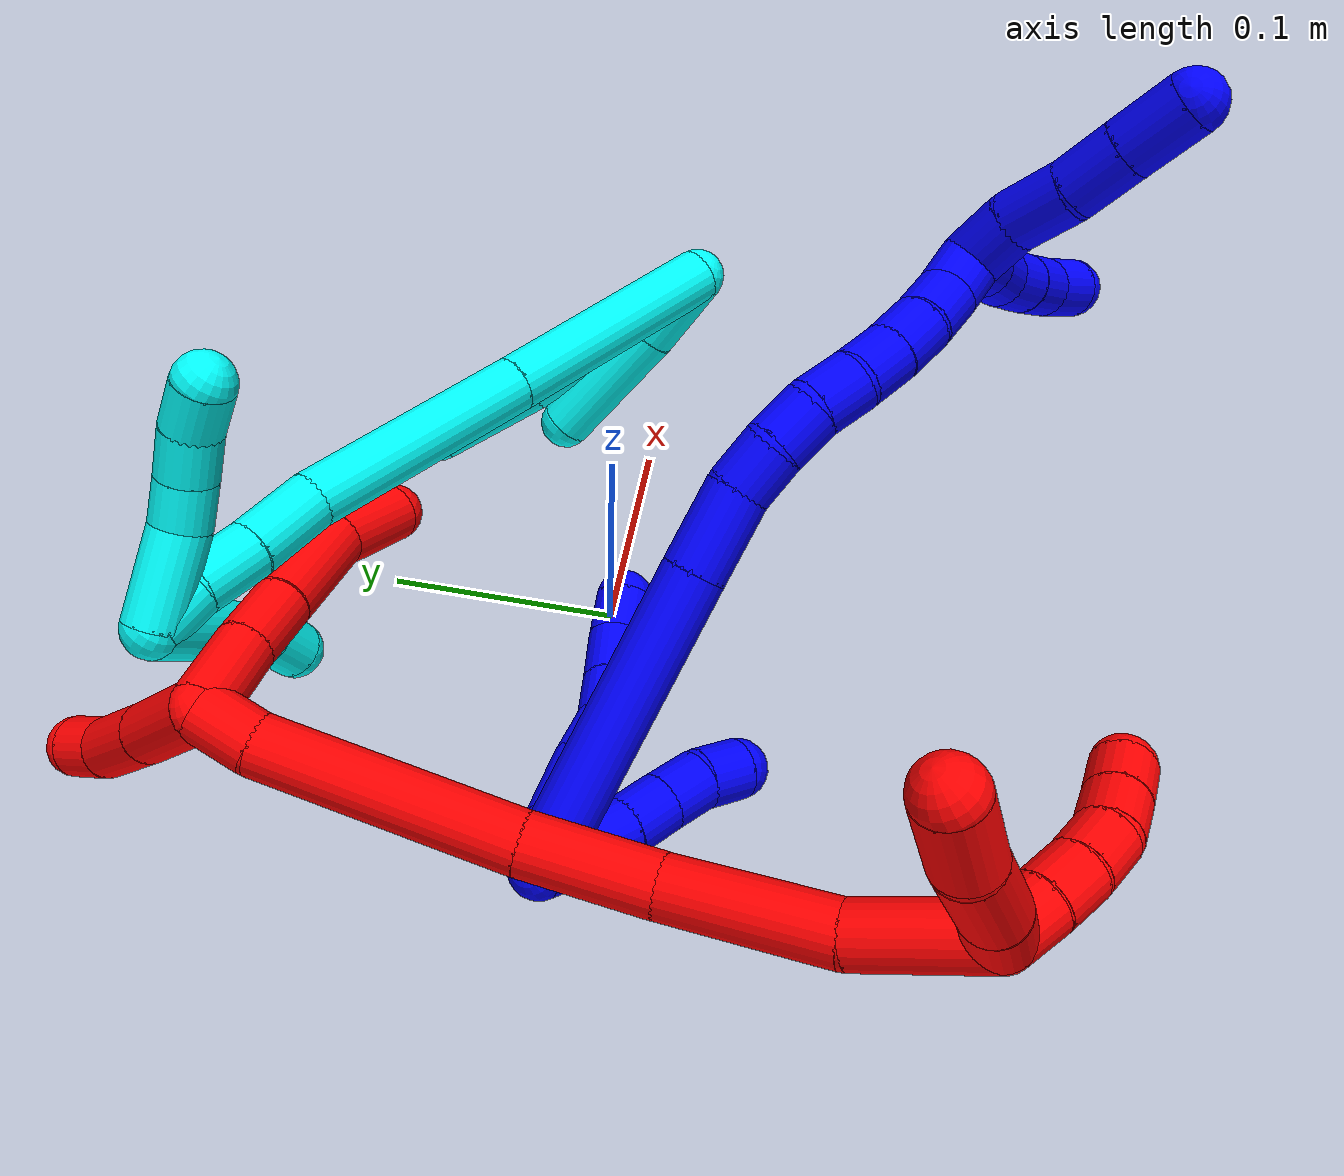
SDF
<sdf version="1.7">
 <world name="default">
  <plugin name="TubeGeneratorPlugin" filename="libtube_generator_plugin.so"/>
  <model name="photoneo_s_sensor">
   <static>1</static>
   <pose>0 0 2 1.57079 1.57079 3.14159</pose>
   <link name="link">
    <inertial><mass>0.1</mass></inertial>
    <sensor name="sensor" type="depth">
     <update_rate>30</update_rate>
     <camera>
      <horizontal_fov>1.22</horizontal_fov>
      <image><width>1920</width><height>1200</height><format>B8G8R8</format></image>
      <clip><near>0.1</near><far>4</far></clip>
      <depth_camera><output>points</output></depth_camera>
     </camera>
     <plugin name="camera_plugin" filename="libgazebo_ros_depth_camera.so">
      <baseline>0.2</baseline>
      <alwaysOn>1</alwaysOn>
      <updateRate>0.0</updateRate>
      <cameraName>camera_ir</cameraName>
      <imageTopicName>/camera/color/image_raw</imageTopicName>
      <cameraInfoTopicName>/camera/color/camera_info</cameraInfoTopicName>
      <depthImageTopicName>/camera/depth/image_raw</depthImageTopicName>
      <depthImageCameraInfoTopicName>/camera/depth/camera_info</depthImageCameraInfoTopicName>
      <pointCloudTopicName>/camera/depth/points</pointCloudTopicName>
      <frameName>fr_optical</frameName>
      <pointCloudCutoff>0.1</pointCloudCutoff>
      <pointCloudCutoffMax>2.0</pointCloudCutoffMax>
      <distortionK1>0</distortionK1>
      <distortionK2>0</distortionK2>
      <distortionK3>0</distortionK3>
      <distortionT1>0</distortionT1>
      <distortionT2>0</distortionT2>
      <CxPrime>0</CxPrime>
      <Cx>0</Cx>
      <Cy>0</Cy>
      <focalLength>0</focalLength>
      <hackBaseline>0</hackBaseline>
     </plugin>
    </sensor>
   </link>
  </model>
  <gravity>0 0 -9.8</gravity>
  <magnetic_field>6e-06 2.3e-05 -4.2e-05</magnetic_field>
  <atmosphere type="adiabatic"/>
  <physics name="default_physics" default="0" type="ode">
   <max_step_size>0.003</max_step_size>
   <real_time_factor>1</real_time_factor>
   <real_time_update_rate>1000</real_time_update_rate>
   <max_contacts>10000</max_contacts>
   <ode>
    <solver>
     <type>quick</type>
     <iters>100</iters>
     <sor>1.3</sor>
     <use_dynamic_moi_rescaling>0</use_dynamic_moi_rescaling>
    </solver>
    <constraints>
     <contact_max_correcting_vel>0</contact_max_correcting_vel>
     <contact_surface_layer>0.001</contact_surface_layer>
     <cfm>0</cfm>
     <erp>0.2</erp>
    </constraints>
   </ode>
  </physics>
  <scene><ambient>0.4 0.4 0.4 1</ambient><background>0.7 0.7 0.7 1</background><shadows>0</shadows></scene>
  <audio><device>default</device></audio>
  <spherical_coordinates>
   <surface_model>EARTH_WGS84</surface_model>
   <latitude_deg>0</latitude_deg>
   <longitude_deg>0</longitude_deg>
   <elevation>0</elevation>
   <heading_deg>0</heading_deg>
  </spherical_coordinates>
  <model name="bin">
   <static>1</static>
   <link name="bottom">
    <collision name="collision-bottom">
     <pose>0 0 -0.01 0 -0 0</pose>
     <geometry><box><size>0.8 0.6 0.02</size></box></geometry>
     <surface>
      <friction><ode><mu>100</mu><mu2>100</mu2></ode></friction>
      <contact><collide_bitmask>65535</collide_bitmask></contact>
     </surface>
    </collision>
   </link>
   <link name="west_wall">
    <collision name="collision-west_wall">
     <pose>-0.41 0 0.1 0 -0 0</pose>
     <geometry><box><size>0.02 0.6 0.2</size></box></geometry>
     <surface>
      <friction><ode><mu>100</mu><mu2>100</mu2></ode></friction>
      <contact><collide_bitmask>65535</collide_bitmask></contact>
     </surface>
    </collision>
   </link>
   <link name="east_wall">
    <collision name="collision-east_wall">
     <pose>0.41 0 0.1 0 -0 0</pose>
     <geometry><box><size>0.02 0.6 0.2</size></box></geometry>
     <surface>
      <friction><ode><mu>100</mu><mu2>100</mu2></ode></friction>
      <contact><collide_bitmask>65535</collide_bitmask></contact>
     </surface>
    </collision>
   </link>
   <link name="south_wall">
    <collision name="collision-south_wall">
     <pose>0 -0.31 0.1 0 -0 0</pose>
     <geometry><box><size>0.8 0.02 0.2</size></box></geometry>
     <surface>
      <friction><ode><mu>100</mu><mu2>100</mu2></ode></friction>
      <contact><collide_bitmask>65535</collide_bitmask></contact>
     </surface>
    </collision>
   </link>
   <link name="north_wall">
    <collision name="collision-north_wall">
     <pose>0 0.31 0.1 0 -0 0</pose>
     <geometry><box><size>0.8 0.02 0.2</size></box></geometry>
     <surface>
      <friction><ode><mu>100</mu><mu2>100</mu2></ode></friction>
      <contact><collide_bitmask>65535</collide_bitmask></contact>
     </surface>
    </collision>
   </link>
  </model>
  <model name="1">
   <static>0</static>
   <link name="1">
    <collision name="collision-cylinder-e_1_2_8">
     <pose>0.007035 0.00235 -0.008774 -2.87991 0.658958 -2.40685</pose>
     <geometry><cylinder><radius>0.0125</radius><length>0.022978</length></cylinder></geometry>
     <surface>
      <friction><ode><mu>1.16</mu><mu2>1.16</mu2><slip1>0</slip1><slip2>0</slip2></ode></friction>
      <contact><ode><kp>1e+06</kp><kd>1</kd><max_vel>0</max_vel><min_depth>0.001</min_depth></ode></contact>
     </surface>
    </collision>
    <visual name="visual-cylinder-e_1_2_8">
     <pose>0.007035 0.00235 -0.008774 -2.87991 0.658958 -2.40685</pose>
     <geometry><cylinder><radius>0.0125</radius><length>0.022978</length></cylinder></geometry>
     <material><ambient>0 0 1 1</ambient></material>
    </visual>
    <collision name="collision-cylinder-e_2_8_9">
     <pose>0.026515 0.006937 -0.031574 -2.98342 0.719561 -2.72628</pose>
     <geometry><cylinder><radius>0.0125</radius><length>0.037769</length></cylinder></geometry>
     <surface>
      <friction><ode><mu>1.16</mu><mu2>1.16</mu2><slip1>0</slip1><slip2>0</slip2></ode></friction>
      <contact><ode><kp>1e+06</kp><kd>1</kd><max_vel>0</max_vel><min_depth>0.001</min_depth></ode></contact>
     </surface>
    </collision>
    <visual name="visual-cylinder-e_2_8_9">
     <pose>0.026515 0.006937 -0.031574 -2.98342 0.719561 -2.72628</pose>
     <geometry><cylinder><radius>0.0125</radius><length>0.037769</length></cylinder></geometry>
     <material><ambient>0 0 1 1</ambient></material>
    </visual>
    <collision name="collision-cylinder-e_3_9_10">
     <pose>0.047963 0.008152 -0.052252 2.98902 0.928774 2.83875</pose>
     <geometry><cylinder><radius>0.0125</radius><length>0.022479</length></cylinder></geometry>
     <surface>
      <friction><ode><mu>1.16</mu><mu2>1.16</mu2><slip1>0</slip1><slip2>0</slip2></ode></friction>
      <contact><ode><kp>1e+06</kp><kd>1</kd><max_vel>0</max_vel><min_depth>0.001</min_depth></ode></contact>
     </surface>
    </collision>
    <visual name="visual-cylinder-e_3_9_10">
     <pose>0.047963 0.008152 -0.052252 2.98902 0.928774 2.83875</pose>
     <geometry><cylinder><radius>0.0125</radius><length>0.022479</length></cylinder></geometry>
     <material><ambient>0 0 1 1</ambient></material>
    </visual>
    <collision name="collision-cylinder-e_4_10_11">
     <pose>0.065292 0.009802 -0.064951 -2.72537 0.899784 -2.31715</pose>
     <geometry><cylinder><radius>0.0125</radius><length>0.021265</length></cylinder></geometry>
     <surface>
      <friction><ode><mu>1.16</mu><mu2>1.16</mu2><slip1>0</slip1><slip2>0</slip2></ode></friction>
      <contact><ode><kp>1e+06</kp><kd>1</kd><max_vel>0</max_vel><min_depth>0.001</min_depth></ode></contact>
     </surface>
    </collision>
    <visual name="visual-cylinder-e_4_10_11">
     <pose>0.065292 0.009802 -0.064951 -2.72537 0.899784 -2.31715</pose>
     <geometry><cylinder><radius>0.0125</radius><length>0.021265</length></cylinder></geometry>
     <material><ambient>0 0 1 1</ambient></material>
    </visual>
    <collision name="collision-cylinder-e_5_11_12">
     <pose>0.083612 0.015632 -0.077795 -2.70672 0.927309 -2.30947</pose>
     <geometry><cylinder><radius>0.0125</radius><length>0.024981</length></cylinder></geometry>
     <surface>
      <friction><ode><mu>1.16</mu><mu2>1.16</mu2><slip1>0</slip1><slip2>0</slip2></ode></friction>
      <contact><ode><kp>1e+06</kp><kd>1</kd><max_vel>0</max_vel><min_depth>0.001</min_depth></ode></contact>
     </surface>
    </collision>
    <visual name="visual-cylinder-e_5_11_12">
     <pose>0.083612 0.015632 -0.077795 -2.70672 0.927309 -2.30947</pose>
     <geometry><cylinder><radius>0.0125</radius><length>0.024981</length></cylinder></geometry>
     <material><ambient>0 0 1 1</ambient></material>
    </visual>
    <collision name="collision-cylinder-e_6_12_6">
     <pose>0.102989 0.020128 -0.088526 -2.81369 1.1539 -2.64375</pose>
     <geometry><cylinder><radius>0.0125</radius><length>0.020527</length></cylinder></geometry>
     <surface>
      <friction><ode><mu>1.16</mu><mu2>1.16</mu2><slip1>0</slip1><slip2>0</slip2></ode></friction>
      <contact><ode><kp>1e+06</kp><kd>1</kd><max_vel>0</max_vel><min_depth>0.001</min_depth></ode></contact>
     </surface>
    </collision>
    <visual name="visual-cylinder-e_6_12_6">
     <pose>0.102989 0.020128 -0.088526 -2.81369 1.1539 -2.64375</pose>
     <geometry><cylinder><radius>0.0125</radius><length>0.020527</length></cylinder></geometry>
     <material><ambient>0 0 1 1</ambient></material>
    </visual>
    <collision name="collision-cylinder-e_1_2_13">
     <pose>0.004158 -0.005128 -0.007511 2.54255 0.428807 1.22832</pose>
     <geometry><cylinder><radius>0.0125</radius><length>0.02</length></cylinder></geometry>
     <surface>
      <friction><ode><mu>1.16</mu><mu2>1.16</mu2><slip1>0</slip1><slip2>0</slip2></ode></friction>
      <contact><ode><kp>1e+06</kp><kd>1</kd><max_vel>0</max_vel><min_depth>0.001</min_depth></ode></contact>
     </surface>
    </collision>
    <visual name="visual-cylinder-e_1_2_13">
     <pose>0.004158 -0.005128 -0.007511 2.54255 0.428807 1.22832</pose>
     <geometry><cylinder><radius>0.0125</radius><length>0.02</length></cylinder></geometry>
     <material><ambient>0 0 1 1</ambient></material>
    </visual>
    <collision name="collision-cylinder-e_2_13_14">
     <pose>0.012977 -0.014766 -0.022634 2.60675 0.484868 1.4685</pose>
     <geometry><cylinder><radius>0.0125</radius><length>0.02</length></cylinder></geometry>
     <surface>
      <friction><ode><mu>1.16</mu><mu2>1.16</mu2><slip1>0</slip1><slip2>0</slip2></ode></friction>
      <contact><ode><kp>1e+06</kp><kd>1</kd><max_vel>0</max_vel><min_depth>0.001</min_depth></ode></contact>
     </surface>
    </collision>
    <visual name="visual-cylinder-e_2_13_14">
     <pose>0.012977 -0.014766 -0.022634 2.60675 0.484868 1.4685</pose>
     <geometry><cylinder><radius>0.0125</radius><length>0.02</length></cylinder></geometry>
     <material><ambient>0 0 1 1</ambient></material>
    </visual>
    <collision name="collision-cylinder-e_3_14_15">
     <pose>0.023086 -0.023362 -0.037568 2.63249 0.576204 1.70052</pose>
     <geometry><cylinder><radius>0.0125</radius><length>0.02</length></cylinder></geometry>
     <surface>
      <friction><ode><mu>1.16</mu><mu2>1.16</mu2><slip1>0</slip1><slip2>0</slip2></ode></friction>
      <contact><ode><kp>1e+06</kp><kd>1</kd><max_vel>0</max_vel><min_depth>0.001</min_depth></ode></contact>
     </surface>
    </collision>
    <visual name="visual-cylinder-e_3_14_15">
     <pose>0.023086 -0.023362 -0.037568 2.63249 0.576204 1.70052</pose>
     <geometry><cylinder><radius>0.0125</radius><length>0.02</length></cylinder></geometry>
     <material><ambient>0 0 1 1</ambient></material>
    </visual>
    <collision name="collision-cylinder-e_4_15_16">
     <pose>0.033892 -0.031894 -0.052069 2.58724 0.565457 1.59169</pose>
     <geometry><cylinder><radius>0.0125</radius><length>0.02</length></cylinder></geometry>
     <surface>
      <friction><ode><mu>1.16</mu><mu2>1.16</mu2><slip1>0</slip1><slip2>0</slip2></ode></friction>
      <contact><ode><kp>1e+06</kp><kd>1</kd><max_vel>0</max_vel><min_depth>0.001</min_depth></ode></contact>
     </surface>
    </collision>
    <visual name="visual-cylinder-e_4_15_16">
     <pose>0.033892 -0.031894 -0.052069 2.58724 0.565457 1.59169</pose>
     <geometry><cylinder><radius>0.0125</radius><length>0.02</length></cylinder></geometry>
     <material><ambient>0 0 1 1</ambient></material>
    </visual>
    <collision name="collision-cylinder-e_5_16_5">
     <pose>0.042385 -0.041432 -0.067262 2.57546 0.318782 1.00977</pose>
     <geometry><cylinder><radius>0.0125</radius><length>0.02</length></cylinder></geometry>
     <surface>
      <friction><ode><mu>1.16</mu><mu2>1.16</mu2><slip1>0</slip1><slip2>0</slip2></ode></friction>
      <contact><ode><kp>1e+06</kp><kd>1</kd><max_vel>0</max_vel><min_depth>0.001</min_depth></ode></contact>
     </surface>
    </collision>
    <visual name="visual-cylinder-e_5_16_5">
     <pose>0.042385 -0.041432 -0.067262 2.57546 0.318782 1.00977</pose>
     <geometry><cylinder><radius>0.0125</radius><length>0.02</length></cylinder></geometry>
     <material><ambient>0 0 1 1</ambient></material>
    </visual>
    <collision name="collision-cylinder-e_1_2_17">
     <pose>0.057682 -0.02414 0.001893 1.49252 1.17335 1.10225</pose>
     <geometry><cylinder><radius>0.0125</radius><length>0.125116</length></cylinder></geometry>
     <surface>
      <friction><ode><mu>1.16</mu><mu2>1.16</mu2><slip1>0</slip1><slip2>0</slip2></ode></friction>
      <contact><ode><kp>1e+06</kp><kd>1</kd><max_vel>0</max_vel><min_depth>0.001</min_depth></ode></contact>
     </surface>
    </collision>
    <visual name="visual-cylinder-e_1_2_17">
     <pose>0.057682 -0.02414 0.001893 1.49252 1.17335 1.10225</pose>
     <geometry><cylinder><radius>0.0125</radius><length>0.125116</length></cylinder></geometry>
     <material><ambient>0 0 1 1</ambient></material>
    </visual>
    <collision name="collision-cylinder-e_2_17_18">
     <pose>0.131139 -0.05495 0.004052 1.53109 1.17047 1.13419</pose>
     <geometry><cylinder><radius>0.0125</radius><length>0.034259</length></cylinder></geometry>
     <surface>
      <friction><ode><mu>1.16</mu><mu2>1.16</mu2><slip1>0</slip1><slip2>0</slip2></ode></friction>
      <contact><ode><kp>1e+06</kp><kd>1</kd><max_vel>0</max_vel><min_depth>0.001</min_depth></ode></contact>
     </surface>
    </collision>
    <visual name="visual-cylinder-e_2_17_18">
     <pose>0.131139 -0.05495 0.004052 1.53109 1.17047 1.13419</pose>
     <geometry><cylinder><radius>0.0125</radius><length>0.034259</length></cylinder></geometry>
     <material><ambient>0 0 1 1</ambient></material>
    </visual>
    <collision name="collision-cylinder-e_3_18_19">
     <pose>0.155313 -0.067552 0.004344 1.56622 0.955907 0.952176</pose>
     <geometry><cylinder><radius>0.0125</radius><length>0.020565</length></cylinder></geometry>
     <surface>
      <friction><ode><mu>1.16</mu><mu2>1.16</mu2><slip1>0</slip1><slip2>0</slip2></ode></friction>
      <contact><ode><kp>1e+06</kp><kd>1</kd><max_vel>0</max_vel><min_depth>0.001</min_depth></ode></contact>
     </surface>
    </collision>
    <visual name="visual-cylinder-e_3_18_19">
     <pose>0.155313 -0.067552 0.004344 1.56622 0.955907 0.952176</pose>
     <geometry><cylinder><radius>0.0125</radius><length>0.020565</length></cylinder></geometry>
     <material><ambient>0 0 1 1</ambient></material>
    </visual>
    <collision name="collision-cylinder-e_4_19_20">
     <pose>0.171654 -0.079183 0.002193 1.93584 0.915689 1.24257</pose>
     <geometry><cylinder><radius>0.0125</radius><length>0.020029</length></cylinder></geometry>
     <surface>
      <friction><ode><mu>1.16</mu><mu2>1.16</mu2><slip1>0</slip1><slip2>0</slip2></ode></friction>
      <contact><ode><kp>1e+06</kp><kd>1</kd><max_vel>0</max_vel><min_depth>0.001</min_depth></ode></contact>
     </surface>
    </collision>
    <visual name="visual-cylinder-e_4_19_20">
     <pose>0.171654 -0.079183 0.002193 1.93584 0.915689 1.24257</pose>
     <geometry><cylinder><radius>0.0125</radius><length>0.020029</length></cylinder></geometry>
     <material><ambient>0 0 1 1</ambient></material>
    </visual>
    <collision name="collision-cylinder-e_5_20_21">
     <pose>0.186323 -0.090768 -0.004477 2.22273 0.737605 1.32632</pose>
     <geometry><cylinder><radius>0.0125</radius><length>0.020009</length></cylinder></geometry>
     <surface>
      <friction><ode><mu>1.16</mu><mu2>1.16</mu2><slip1>0</slip1><slip2>0</slip2></ode></friction>
      <contact><ode><kp>1e+06</kp><kd>1</kd><max_vel>0</max_vel><min_depth>0.001</min_depth></ode></contact>
     </surface>
    </collision>
    <visual name="visual-cylinder-e_5_20_21">
     <pose>0.186323 -0.090768 -0.004477 2.22273 0.737605 1.32632</pose>
     <geometry><cylinder><radius>0.0125</radius><length>0.020009</length></cylinder></geometry>
     <material><ambient>0 0 1 1</ambient></material>
    </visual>
    <collision name="collision-cylinder-e_6_21_22">
     <pose>0.199889 -0.101075 -0.014793 2.49221 0.751877 1.72938</pose>
     <geometry><cylinder><radius>0.0125</radius><length>0.020022</length></cylinder></geometry>
     <surface>
      <friction><ode><mu>1.16</mu><mu2>1.16</mu2><slip1>0</slip1><slip2>0</slip2></ode></friction>
      <contact><ode><kp>1e+06</kp><kd>1</kd><max_vel>0</max_vel><min_depth>0.001</min_depth></ode></contact>
     </surface>
    </collision>
    <visual name="visual-cylinder-e_6_21_22">
     <pose>0.199889 -0.101075 -0.014793 2.49221 0.751877 1.72938</pose>
     <geometry><cylinder><radius>0.0125</radius><length>0.020022</length></cylinder></geometry>
     <material><ambient>0 0 1 1</ambient></material>
    </visual>
    <collision name="collision-cylinder-e_7_22_23">
     <pose>0.214139 -0.109443 -0.026046 2.51304 0.834922 1.87671</pose>
     <geometry><cylinder><radius>0.0125</radius><length>0.02</length></cylinder></geometry>
     <surface>
      <friction><ode><mu>1.16</mu><mu2>1.16</mu2><slip1>0</slip1><slip2>0</slip2></ode></friction>
      <contact><ode><kp>1e+06</kp><kd>1</kd><max_vel>0</max_vel><min_depth>0.001</min_depth></ode></contact>
     </surface>
    </collision>
    <visual name="visual-cylinder-e_7_22_23">
     <pose>0.214139 -0.109443 -0.026046 2.51304 0.834922 1.87671</pose>
     <geometry><cylinder><radius>0.0125</radius><length>0.02</length></cylinder></geometry>
     <material><ambient>0 0 1 1</ambient></material>
    </visual>
    <collision name="collision-cylinder-e_8_23_24">
     <pose>0.229105 -0.115964 -0.037502 2.73783 0.85621 2.29836</pose>
     <geometry><cylinder><radius>0.0125</radius><length>0.02</length></cylinder></geometry>
     <surface>
      <friction><ode><mu>1.16</mu><mu2>1.16</mu2><slip1>0</slip1><slip2>0</slip2></ode></friction>
      <contact><ode><kp>1e+06</kp><kd>1</kd><max_vel>0</max_vel><min_depth>0.001</min_depth></ode></contact>
     </surface>
    </collision>
    <visual name="visual-cylinder-e_8_23_24">
     <pose>0.229105 -0.115964 -0.037502 2.73783 0.85621 2.29836</pose>
     <geometry><cylinder><radius>0.0125</radius><length>0.02</length></cylinder></geometry>
     <material><ambient>0 0 1 1</ambient></material>
    </visual>
    <collision name="collision-cylinder-e_9_24_1">
     <pose>0.245128 -0.121498 -0.047946 2.55129 1.01019 2.13613</pose>
     <geometry><cylinder><radius>0.0125</radius><length>0.02</length></cylinder></geometry>
     <surface>
      <friction><ode><mu>1.16</mu><mu2>1.16</mu2><slip1>0</slip1><slip2>0</slip2></ode></friction>
      <contact><ode><kp>1e+06</kp><kd>1</kd><max_vel>0</max_vel><min_depth>0.001</min_depth></ode></contact>
     </surface>
    </collision>
    <visual name="visual-cylinder-e_9_24_1">
     <pose>0.245128 -0.121498 -0.047946 2.55129 1.01019 2.13613</pose>
     <geometry><cylinder><radius>0.0125</radius><length>0.02</length></cylinder></geometry>
     <material><ambient>0 0 1 1</ambient></material>
    </visual>
    <collision name="collision-cylinder-e_1_1_25">
     <pose>0.25573 -0.124941 -0.062121 3.09217 0.214954 2.69121</pose>
     <geometry><cylinder><radius>0.0125</radius><length>0.02</length></cylinder></geometry>
     <surface>
      <friction><ode><mu>1.16</mu><mu2>1.16</mu2><slip1>0</slip1><slip2>0</slip2></ode></friction>
      <contact><ode><kp>1e+06</kp><kd>1</kd><max_vel>0</max_vel><min_depth>0.001</min_depth></ode></contact>
     </surface>
    </collision>
    <visual name="visual-cylinder-e_1_1_25">
     <pose>0.25573 -0.124941 -0.062121 3.09217 0.214954 2.69121</pose>
     <geometry><cylinder><radius>0.0125</radius><length>0.02</length></cylinder></geometry>
     <material><ambient>0 0 1 1</ambient></material>
    </visual>
    <collision name="collision-cylinder-e_2_25_26">
     <pose>0.25909 -0.126614 -0.081731 3.02136 0.122963 1.59331</pose>
     <geometry><cylinder><radius>0.0125</radius><length>0.02</length></cylinder></geometry>
     <surface>
      <friction><ode><mu>1.16</mu><mu2>1.16</mu2><slip1>0</slip1><slip2>0</slip2></ode></friction>
      <contact><ode><kp>1e+06</kp><kd>1</kd><max_vel>0</max_vel><min_depth>0.001</min_depth></ode></contact>
     </surface>
    </collision>
    <visual name="visual-cylinder-e_2_25_26">
     <pose>0.25909 -0.126614 -0.081731 3.02136 0.122963 1.59331</pose>
     <geometry><cylinder><radius>0.0125</radius><length>0.02</length></cylinder></geometry>
     <material><ambient>0 0 1 1</ambient></material>
    </visual>
    <collision name="collision-cylinder-e_3_26_27">
     <pose>0.261925 -0.130824 -0.100981 2.83057 0.161536 0.953193</pose>
     <geometry><cylinder><radius>0.0125</radius><length>0.02</length></cylinder></geometry>
     <surface>
      <friction><ode><mu>1.16</mu><mu2>1.16</mu2><slip1>0</slip1><slip2>0</slip2></ode></friction>
      <contact><ode><kp>1e+06</kp><kd>1</kd><max_vel>0</max_vel><min_depth>0.001</min_depth></ode></contact>
     </surface>
    </collision>
    <visual name="visual-cylinder-e_3_26_27">
     <pose>0.261925 -0.130824 -0.100981 2.83057 0.161536 0.953193</pose>
     <geometry><cylinder><radius>0.0125</radius><length>0.02</length></cylinder></geometry>
     <material><ambient>0 0 1 1</ambient></material>
    </visual>
    <collision name="collision-cylinder-e_4_27_28">
     <pose>0.265727 -0.136576 -0.119743 2.85784 0.22123 1.32184</pose>
     <geometry><cylinder><radius>0.0125</radius><length>0.02</length></cylinder></geometry>
     <surface>
      <friction><ode><mu>1.16</mu><mu2>1.16</mu2><slip1>0</slip1><slip2>0</slip2></ode></friction>
      <contact><ode><kp>1e+06</kp><kd>1</kd><max_vel>0</max_vel><min_depth>0.001</min_depth></ode></contact>
     </surface>
    </collision>
    <visual name="visual-cylinder-e_4_27_28">
     <pose>0.265727 -0.136576 -0.119743 2.85784 0.22123 1.32184</pose>
     <geometry><cylinder><radius>0.0125</radius><length>0.02</length></cylinder></geometry>
     <material><ambient>0 0 1 1</ambient></material>
    </visual>
    <collision name="collision-cylinder-e_5_28_4">
     <pose>0.270432 -0.143847 -0.137659 2.65352 0.253734 0.946814</pose>
     <geometry><cylinder><radius>0.0125</radius><length>0.02</length></cylinder></geometry>
     <surface>
      <friction><ode><mu>1.16</mu><mu2>1.16</mu2><slip1>0</slip1><slip2>0</slip2></ode></friction>
      <contact><ode><kp>1e+06</kp><kd>1</kd><max_vel>0</max_vel><min_depth>0.001</min_depth></ode></contact>
     </surface>
    </collision>
    <visual name="visual-cylinder-e_5_28_4">
     <pose>0.270432 -0.143847 -0.137659 2.65352 0.253734 0.946814</pose>
     <geometry><cylinder><radius>0.0125</radius><length>0.02</length></cylinder></geometry>
     <material><ambient>0 0 1 1</ambient></material>
    </visual>
    <collision name="collision-cylinder-e_1_1_29">
     <pose>0.259709 -0.132955 -0.047726 1.07132 0.563147 0.34006</pose>
     <geometry><cylinder><radius>0.0125</radius><length>0.022896</length></cylinder></geometry>
     <surface>
      <friction><ode><mu>1.16</mu><mu2>1.16</mu2><slip1>0</slip1><slip2>0</slip2></ode></friction>
      <contact><ode><kp>1e+06</kp><kd>1</kd><max_vel>0</max_vel><min_depth>0.001</min_depth></ode></contact>
     </surface>
    </collision>
    <visual name="visual-cylinder-e_1_1_29">
     <pose>0.259709 -0.132955 -0.047726 1.07132 0.563147 0.34006</pose>
     <geometry><cylinder><radius>0.0125</radius><length>0.022896</length></cylinder></geometry>
     <material><ambient>0 0 1 1</ambient></material>
    </visual>
    <collision name="collision-cylinder-e_2_29_30">
     <pose>0.269891 -0.152583 -0.037892 1.13387 0.320006 0.204771</pose>
     <geometry><cylinder><radius>0.0125</radius><length>0.025883</length></cylinder></geometry>
     <surface>
      <friction><ode><mu>1.16</mu><mu2>1.16</mu2><slip1>0</slip1><slip2>0</slip2></ode></friction>
      <contact><ode><kp>1e+06</kp><kd>1</kd><max_vel>0</max_vel><min_depth>0.001</min_depth></ode></contact>
     </surface>
    </collision>
    <visual name="visual-cylinder-e_2_29_30">
     <pose>0.269891 -0.152583 -0.037892 1.13387 0.320006 0.204771</pose>
     <geometry><cylinder><radius>0.0125</radius><length>0.025883</length></cylinder></geometry>
     <material><ambient>0 0 1 1</ambient></material>
    </visual>
    <collision name="collision-cylinder-e_3_30_31">
     <pose>0.279603 -0.1735 -0.028144 1.13567 0.481623 0.31079</pose>
     <geometry><cylinder><radius>0.0125</radius><length>0.024354</length></cylinder></geometry>
     <surface>
      <friction><ode><mu>1.16</mu><mu2>1.16</mu2><slip1>0</slip1><slip2>0</slip2></ode></friction>
      <contact><ode><kp>1e+06</kp><kd>1</kd><max_vel>0</max_vel><min_depth>0.001</min_depth></ode></contact>
     </surface>
    </collision>
    <visual name="visual-cylinder-e_3_30_31">
     <pose>0.279603 -0.1735 -0.028144 1.13567 0.481623 0.31079</pose>
     <geometry><cylinder><radius>0.0125</radius><length>0.024354</length></cylinder></geometry>
     <material><ambient>0 0 1 1</ambient></material>
    </visual>
    <collision name="collision-cylinder-e_4_31_3">
     <pose>0.291373 -0.194171 -0.018654 1.14464 0.473814 0.308623</pose>
     <geometry><cylinder><radius>0.0125</radius><length>0.026867</length></cylinder></geometry>
     <surface>
      <friction><ode><mu>1.16</mu><mu2>1.16</mu2><slip1>0</slip1><slip2>0</slip2></ode></friction>
      <contact><ode><kp>1e+06</kp><kd>1</kd><max_vel>0</max_vel><min_depth>0.001</min_depth></ode></contact>
     </surface>
    </collision>
    <visual name="visual-cylinder-e_4_31_3">
     <pose>0.291373 -0.194171 -0.018654 1.14464 0.473814 0.308623</pose>
     <geometry><cylinder><radius>0.0125</radius><length>0.026867</length></cylinder></geometry>
     <material><ambient>0 0 1 1</ambient></material>
    </visual>
    <collision name="collision-sphere-3">
     <pose>0.297503 -0.205055 -0.013713 0 -0 0</pose>
     <geometry><sphere><radius>0.0125</radius></sphere></geometry>
     <surface>
      <friction><ode><mu>1.16</mu><mu2>1.16</mu2><slip1>0</slip1><slip2>0</slip2></ode></friction>
      <contact><ode><kp>1e+06</kp><kd>1</kd><max_vel>0</max_vel><min_depth>0.001</min_depth></ode></contact>
     </surface>
    </collision>
    <visual name="visual-sphere-3">
     <pose>0.297503 -0.205055 -0.013713 0 -0 0</pose>
     <geometry><sphere><radius>0.0125</radius></sphere></geometry>
     <material><ambient>0 0 1 1</ambient></material>
    </visual>
    <collision name="collision-sphere-31">
     <pose>0.285244 -0.183286 -0.023595 0 -0 0</pose>
     <geometry><sphere><radius>0.0125</radius></sphere></geometry>
     <surface>
      <friction><ode><mu>1.16</mu><mu2>1.16</mu2><slip1>0</slip1><slip2>0</slip2></ode></friction>
      <contact><ode><kp>1e+06</kp><kd>1</kd><max_vel>0</max_vel><min_depth>0.001</min_depth></ode></contact>
     </surface>
    </collision>
    <visual name="visual-sphere-31">
     <pose>0.285244 -0.183286 -0.023595 0 -0 0</pose>
     <geometry><sphere><radius>0.0125</radius></sphere></geometry>
     <material><ambient>0 0 1 1</ambient></material>
    </visual>
    <collision name="collision-sphere-30">
     <pose>0.273962 -0.163713 -0.032693 0 -0 0</pose>
     <geometry><sphere><radius>0.0125</radius></sphere></geometry>
     <surface>
      <friction><ode><mu>1.16</mu><mu2>1.16</mu2><slip1>0</slip1><slip2>0</slip2></ode></friction>
      <contact><ode><kp>1e+06</kp><kd>1</kd><max_vel>0</max_vel><min_depth>0.001</min_depth></ode></contact>
     </surface>
    </collision>
    <visual name="visual-sphere-30">
     <pose>0.273962 -0.163713 -0.032693 0 -0 0</pose>
     <geometry><sphere><radius>0.0125</radius></sphere></geometry>
     <material><ambient>0 0 1 1</ambient></material>
    </visual>
    <collision name="collision-sphere-29">
     <pose>0.26582 -0.141453 -0.04309 0 -0 0</pose>
     <geometry><sphere><radius>0.0125</radius></sphere></geometry>
     <surface>
      <friction><ode><mu>1.16</mu><mu2>1.16</mu2><slip1>0</slip1><slip2>0</slip2></ode></friction>
      <contact><ode><kp>1e+06</kp><kd>1</kd><max_vel>0</max_vel><min_depth>0.001</min_depth></ode></contact>
     </surface>
    </collision>
    <visual name="visual-sphere-29">
     <pose>0.26582 -0.141453 -0.04309 0 -0 0</pose>
     <geometry><sphere><radius>0.0125</radius></sphere></geometry>
     <material><ambient>0 0 1 1</ambient></material>
    </visual>
    <collision name="collision-sphere-4">
     <pose>0.272942 -0.148386 -0.146208 0 -0 0</pose>
     <geometry><sphere><radius>0.0125</radius></sphere></geometry>
     <surface>
      <friction><ode><mu>1.16</mu><mu2>1.16</mu2><slip1>0</slip1><slip2>0</slip2></ode></friction>
      <contact><ode><kp>1e+06</kp><kd>1</kd><max_vel>0</max_vel><min_depth>0.001</min_depth></ode></contact>
     </surface>
    </collision>
    <visual name="visual-sphere-4">
     <pose>0.272942 -0.148386 -0.146208 0 -0 0</pose>
     <geometry><sphere><radius>0.0125</radius></sphere></geometry>
     <material><ambient>0 0 1 1</ambient></material>
    </visual>
    <collision name="collision-sphere-28">
     <pose>0.267922 -0.139308 -0.129109 0 -0 0</pose>
     <geometry><sphere><radius>0.0125</radius></sphere></geometry>
     <surface>
      <friction><ode><mu>1.16</mu><mu2>1.16</mu2><slip1>0</slip1><slip2>0</slip2></ode></friction>
      <contact><ode><kp>1e+06</kp><kd>1</kd><max_vel>0</max_vel><min_depth>0.001</min_depth></ode></contact>
     </surface>
    </collision>
    <visual name="visual-sphere-28">
     <pose>0.267922 -0.139308 -0.129109 0 -0 0</pose>
     <geometry><sphere><radius>0.0125</radius></sphere></geometry>
     <material><ambient>0 0 1 1</ambient></material>
    </visual>
    <collision name="collision-sphere-27">
     <pose>0.263533 -0.133845 -0.110377 0 -0 0</pose>
     <geometry><sphere><radius>0.0125</radius></sphere></geometry>
     <surface>
      <friction><ode><mu>1.16</mu><mu2>1.16</mu2><slip1>0</slip1><slip2>0</slip2></ode></friction>
      <contact><ode><kp>1e+06</kp><kd>1</kd><max_vel>0</max_vel><min_depth>0.001</min_depth></ode></contact>
     </surface>
    </collision>
    <visual name="visual-sphere-27">
     <pose>0.263533 -0.133845 -0.110377 0 -0 0</pose>
     <geometry><sphere><radius>0.0125</radius></sphere></geometry>
     <material><ambient>0 0 1 1</ambient></material>
    </visual>
    <collision name="collision-sphere-26">
     <pose>0.260316 -0.127804 -0.091584 0 -0 0</pose>
     <geometry><sphere><radius>0.0125</radius></sphere></geometry>
     <surface>
      <friction><ode><mu>1.16</mu><mu2>1.16</mu2><slip1>0</slip1><slip2>0</slip2></ode></friction>
      <contact><ode><kp>1e+06</kp><kd>1</kd><max_vel>0</max_vel><min_depth>0.001</min_depth></ode></contact>
     </surface>
    </collision>
    <visual name="visual-sphere-26">
     <pose>0.260316 -0.127804 -0.091584 0 -0 0</pose>
     <geometry><sphere><radius>0.0125</radius></sphere></geometry>
     <material><ambient>0 0 1 1</ambient></material>
    </visual>
    <collision name="collision-sphere-25">
     <pose>0.257863 -0.125423 -0.071879 0 -0 0</pose>
     <geometry><sphere><radius>0.0125</radius></sphere></geometry>
     <surface>
      <friction><ode><mu>1.16</mu><mu2>1.16</mu2><slip1>0</slip1><slip2>0</slip2></ode></friction>
      <contact><ode><kp>1e+06</kp><kd>1</kd><max_vel>0</max_vel><min_depth>0.001</min_depth></ode></contact>
     </surface>
    </collision>
    <visual name="visual-sphere-25">
     <pose>0.257863 -0.125423 -0.071879 0 -0 0</pose>
     <geometry><sphere><radius>0.0125</radius></sphere></geometry>
     <material><ambient>0 0 1 1</ambient></material>
    </visual>
    <collision name="collision-sphere-1">
     <pose>0.253597 -0.124458 -0.052363 0 -0 0</pose>
     <geometry><sphere><radius>0.0125</radius></sphere></geometry>
     <surface>
      <friction><ode><mu>1.16</mu><mu2>1.16</mu2><slip1>0</slip1><slip2>0</slip2></ode></friction>
      <contact><ode><kp>1e+06</kp><kd>1</kd><max_vel>0</max_vel><min_depth>0.001</min_depth></ode></contact>
     </surface>
    </collision>
    <visual name="visual-sphere-1">
     <pose>0.253597 -0.124458 -0.052363 0 -0 0</pose>
     <geometry><sphere><radius>0.0125</radius></sphere></geometry>
     <material><ambient>0 0 1 1</ambient></material>
    </visual>
    <collision name="collision-sphere-24">
     <pose>0.236659 -0.118539 -0.043528 0 -0 0</pose>
     <geometry><sphere><radius>0.0125</radius></sphere></geometry>
     <surface>
      <friction><ode><mu>1.16</mu><mu2>1.16</mu2><slip1>0</slip1><slip2>0</slip2></ode></friction>
      <contact><ode><kp>1e+06</kp><kd>1</kd><max_vel>0</max_vel><min_depth>0.001</min_depth></ode></contact>
     </surface>
    </collision>
    <visual name="visual-sphere-24">
     <pose>0.236659 -0.118539 -0.043528 0 -0 0</pose>
     <geometry><sphere><radius>0.0125</radius></sphere></geometry>
     <material><ambient>0 0 1 1</ambient></material>
    </visual>
    <collision name="collision-sphere-23">
     <pose>0.221551 -0.11339 -0.031476 0 -0 0</pose>
     <geometry><sphere><radius>0.0125</radius></sphere></geometry>
     <surface>
      <friction><ode><mu>1.16</mu><mu2>1.16</mu2><slip1>0</slip1><slip2>0</slip2></ode></friction>
      <contact><ode><kp>1e+06</kp><kd>1</kd><max_vel>0</max_vel><min_depth>0.001</min_depth></ode></contact>
     </surface>
    </collision>
    <visual name="visual-sphere-23">
     <pose>0.221551 -0.11339 -0.031476 0 -0 0</pose>
     <geometry><sphere><radius>0.0125</radius></sphere></geometry>
     <material><ambient>0 0 1 1</ambient></material>
    </visual>
    <collision name="collision-sphere-22">
     <pose>0.206726 -0.105496 -0.020617 0 -0 0</pose>
     <geometry><sphere><radius>0.0125</radius></sphere></geometry>
     <surface>
      <friction><ode><mu>1.16</mu><mu2>1.16</mu2><slip1>0</slip1><slip2>0</slip2></ode></friction>
      <contact><ode><kp>1e+06</kp><kd>1</kd><max_vel>0</max_vel><min_depth>0.001</min_depth></ode></contact>
     </surface>
    </collision>
    <visual name="visual-sphere-22">
     <pose>0.206726 -0.105496 -0.020617 0 -0 0</pose>
     <geometry><sphere><radius>0.0125</radius></sphere></geometry>
     <material><ambient>0 0 1 1</ambient></material>
    </visual>
    <collision name="collision-sphere-21">
     <pose>0.193051 -0.096653 -0.008969 0 -0 0</pose>
     <geometry><sphere><radius>0.0125</radius></sphere></geometry>
     <surface>
      <friction><ode><mu>1.16</mu><mu2>1.16</mu2><slip1>0</slip1><slip2>0</slip2></ode></friction>
      <contact><ode><kp>1e+06</kp><kd>1</kd><max_vel>0</max_vel><min_depth>0.001</min_depth></ode></contact>
     </surface>
    </collision>
    <visual name="visual-sphere-21">
     <pose>0.193051 -0.096653 -0.008969 0 -0 0</pose>
     <geometry><sphere><radius>0.0125</radius></sphere></geometry>
     <material><ambient>0 0 1 1</ambient></material>
    </visual>
    <collision name="collision-sphere-12">
     <pose>0.093604 0.018789 -0.084591 0 -0 0</pose>
     <geometry><sphere><radius>0.0125</radius></sphere></geometry>
     <surface>
      <friction><ode><mu>1.16</mu><mu2>1.16</mu2><slip1>0</slip1><slip2>0</slip2></ode></friction>
      <contact><ode><kp>1e+06</kp><kd>1</kd><max_vel>0</max_vel><min_depth>0.001</min_depth></ode></contact>
     </surface>
    </collision>
    <visual name="visual-sphere-12">
     <pose>0.093604 0.018789 -0.084591 0 -0 0</pose>
     <geometry><sphere><radius>0.0125</radius></sphere></geometry>
     <material><ambient>0 0 1 1</ambient></material>
    </visual>
    <collision name="collision-sphere-11">
     <pose>0.073619 0.012475 -0.070998 0 -0 0</pose>
     <geometry><sphere><radius>0.0125</radius></sphere></geometry>
     <surface>
      <friction><ode><mu>1.16</mu><mu2>1.16</mu2><slip1>0</slip1><slip2>0</slip2></ode></friction>
      <contact><ode><kp>1e+06</kp><kd>1</kd><max_vel>0</max_vel><min_depth>0.001</min_depth></ode></contact>
     </surface>
    </collision>
    <visual name="visual-sphere-11">
     <pose>0.073619 0.012475 -0.070998 0 -0 0</pose>
     <geometry><sphere><radius>0.0125</radius></sphere></geometry>
     <material><ambient>0 0 1 1</ambient></material>
    </visual>
    <collision name="collision-sphere-10">
     <pose>0.056964 0.007129 -0.058905 0 -0 0</pose>
     <geometry><sphere><radius>0.0125</radius></sphere></geometry>
     <surface>
      <friction><ode><mu>1.16</mu><mu2>1.16</mu2><slip1>0</slip1><slip2>0</slip2></ode></friction>
      <contact><ode><kp>1e+06</kp><kd>1</kd><max_vel>0</max_vel><min_depth>0.001</min_depth></ode></contact>
     </surface>
    </collision>
    <visual name="visual-sphere-10">
     <pose>0.056964 0.007129 -0.058905 0 -0 0</pose>
     <geometry><sphere><radius>0.0125</radius></sphere></geometry>
     <material><ambient>0 0 1 1</ambient></material>
    </visual>
    <collision name="collision-sphere-9">
     <pose>0.038961 0.009174 -0.0456 0 -0 0</pose>
     <geometry><sphere><radius>0.0125</radius></sphere></geometry>
     <surface>
      <friction><ode><mu>1.16</mu><mu2>1.16</mu2><slip1>0</slip1><slip2>0</slip2></ode></friction>
      <contact><ode><kp>1e+06</kp><kd>1</kd><max_vel>0</max_vel><min_depth>0.001</min_depth></ode></contact>
     </surface>
    </collision>
    <visual name="visual-sphere-9">
     <pose>0.038961 0.009174 -0.0456 0 -0 0</pose>
     <geometry><sphere><radius>0.0125</radius></sphere></geometry>
     <material><ambient>0 0 1 1</ambient></material>
    </visual>
    <collision name="collision-sphere-2">
     <geometry><sphere><radius>0.0125</radius></sphere></geometry>
     <surface>
      <friction><ode><mu>1.16</mu><mu2>1.16</mu2><slip1>0</slip1><slip2>0</slip2></ode></friction>
      <contact><ode><kp>1e+06</kp><kd>1</kd><max_vel>0</max_vel><min_depth>0.001</min_depth></ode></contact>
     </surface>
    </collision>
    <visual name="visual-sphere-2">
     <geometry><sphere><radius>0.0125</radius></sphere></geometry>
     <material><ambient>0 0 1 1</ambient></material>
    </visual>
    <collision name="collision-sphere-19">
     <pose>0.163713 -0.073484 0.004371 0 -0 0</pose>
     <geometry><sphere><radius>0.0125</radius></sphere></geometry>
     <surface>
      <friction><ode><mu>1.16</mu><mu2>1.16</mu2><slip1>0</slip1><slip2>0</slip2></ode></friction>
      <contact><ode><kp>1e+06</kp><kd>1</kd><max_vel>0</max_vel><min_depth>0.001</min_depth></ode></contact>
     </surface>
    </collision>
    <visual name="visual-sphere-19">
     <pose>0.163713 -0.073484 0.004371 0 -0 0</pose>
     <geometry><sphere><radius>0.0125</radius></sphere></geometry>
     <material><ambient>0 0 1 1</ambient></material>
    </visual>
    <collision name="collision-sphere-8">
     <pose>0.014069 0.0047 -0.017549 0 -0 0</pose>
     <geometry><sphere><radius>0.0125</radius></sphere></geometry>
     <surface>
      <friction><ode><mu>1.16</mu><mu2>1.16</mu2><slip1>0</slip1><slip2>0</slip2></ode></friction>
      <contact><ode><kp>1e+06</kp><kd>1</kd><max_vel>0</max_vel><min_depth>0.001</min_depth></ode></contact>
     </surface>
    </collision>
    <visual name="visual-sphere-8">
     <pose>0.014069 0.0047 -0.017549 0 -0 0</pose>
     <geometry><sphere><radius>0.0125</radius></sphere></geometry>
     <material><ambient>0 0 1 1</ambient></material>
    </visual>
    <collision name="collision-sphere-6">
     <pose>0.112373 0.021466 -0.09246 0 -0 0</pose>
     <geometry><sphere><radius>0.0125</radius></sphere></geometry>
     <surface>
      <friction><ode><mu>1.16</mu><mu2>1.16</mu2><slip1>0</slip1><slip2>0</slip2></ode></friction>
      <contact><ode><kp>1e+06</kp><kd>1</kd><max_vel>0</max_vel><min_depth>0.001</min_depth></ode></contact>
     </surface>
    </collision>
    <visual name="visual-sphere-6">
     <pose>0.112373 0.021466 -0.09246 0 -0 0</pose>
     <geometry><sphere><radius>0.0125</radius></sphere></geometry>
     <material><ambient>0 0 1 1</ambient></material>
    </visual>
    <collision name="collision-sphere-13">
     <pose>0.008316 -0.010256 -0.015022 0 -0 0</pose>
     <geometry><sphere><radius>0.0125</radius></sphere></geometry>
     <surface>
      <friction><ode><mu>1.16</mu><mu2>1.16</mu2><slip1>0</slip1><slip2>0</slip2></ode></friction>
      <contact><ode><kp>1e+06</kp><kd>1</kd><max_vel>0</max_vel><min_depth>0.001</min_depth></ode></contact>
     </surface>
    </collision>
    <visual name="visual-sphere-13">
     <pose>0.008316 -0.010256 -0.015022 0 -0 0</pose>
     <geometry><sphere><radius>0.0125</radius></sphere></geometry>
     <material><ambient>0 0 1 1</ambient></material>
    </visual>
    <collision name="collision-sphere-14">
     <pose>0.017638 -0.019275 -0.030246 0 -0 0</pose>
     <geometry><sphere><radius>0.0125</radius></sphere></geometry>
     <surface>
      <friction><ode><mu>1.16</mu><mu2>1.16</mu2><slip1>0</slip1><slip2>0</slip2></ode></friction>
      <contact><ode><kp>1e+06</kp><kd>1</kd><max_vel>0</max_vel><min_depth>0.001</min_depth></ode></contact>
     </surface>
    </collision>
    <visual name="visual-sphere-14">
     <pose>0.017638 -0.019275 -0.030246 0 -0 0</pose>
     <geometry><sphere><radius>0.0125</radius></sphere></geometry>
     <material><ambient>0 0 1 1</ambient></material>
    </visual>
    <collision name="collision-sphere-15">
     <pose>0.028534 -0.027449 -0.04489 0 -0 0</pose>
     <geometry><sphere><radius>0.0125</radius></sphere></geometry>
     <surface>
      <friction><ode><mu>1.16</mu><mu2>1.16</mu2><slip1>0</slip1><slip2>0</slip2></ode></friction>
      <contact><ode><kp>1e+06</kp><kd>1</kd><max_vel>0</max_vel><min_depth>0.001</min_depth></ode></contact>
     </surface>
    </collision>
    <visual name="visual-sphere-15">
     <pose>0.028534 -0.027449 -0.04489 0 -0 0</pose>
     <geometry><sphere><radius>0.0125</radius></sphere></geometry>
     <material><ambient>0 0 1 1</ambient></material>
    </visual>
    <collision name="collision-sphere-16">
     <pose>0.03925 -0.036338 -0.059248 0 -0 0</pose>
     <geometry><sphere><radius>0.0125</radius></sphere></geometry>
     <surface>
      <friction><ode><mu>1.16</mu><mu2>1.16</mu2><slip1>0</slip1><slip2>0</slip2></ode></friction>
      <contact><ode><kp>1e+06</kp><kd>1</kd><max_vel>0</max_vel><min_depth>0.001</min_depth></ode></contact>
     </surface>
    </collision>
    <visual name="visual-sphere-16">
     <pose>0.03925 -0.036338 -0.059248 0 -0 0</pose>
     <geometry><sphere><radius>0.0125</radius></sphere></geometry>
     <material><ambient>0 0 1 1</ambient></material>
    </visual>
    <collision name="collision-sphere-5">
     <pose>0.045519 -0.046525 -0.075277 0 -0 0</pose>
     <geometry><sphere><radius>0.0125</radius></sphere></geometry>
     <surface>
      <friction><ode><mu>1.16</mu><mu2>1.16</mu2><slip1>0</slip1><slip2>0</slip2></ode></friction>
      <contact><ode><kp>1e+06</kp><kd>1</kd><max_vel>0</max_vel><min_depth>0.001</min_depth></ode></contact>
     </surface>
    </collision>
    <visual name="visual-sphere-5">
     <pose>0.045519 -0.046525 -0.075277 0 -0 0</pose>
     <geometry><sphere><radius>0.0125</radius></sphere></geometry>
     <material><ambient>0 0 1 1</ambient></material>
    </visual>
    <collision name="collision-sphere-17">
     <pose>0.115363 -0.048279 0.003787 0 -0 0</pose>
     <geometry><sphere><radius>0.0125</radius></sphere></geometry>
     <surface>
      <friction><ode><mu>1.16</mu><mu2>1.16</mu2><slip1>0</slip1><slip2>0</slip2></ode></friction>
      <contact><ode><kp>1e+06</kp><kd>1</kd><max_vel>0</max_vel><min_depth>0.001</min_depth></ode></contact>
     </surface>
    </collision>
    <visual name="visual-sphere-17">
     <pose>0.115363 -0.048279 0.003787 0 -0 0</pose>
     <geometry><sphere><radius>0.0125</radius></sphere></geometry>
     <material><ambient>0 0 1 1</ambient></material>
    </visual>
    <collision name="collision-sphere-18">
     <pose>0.146914 -0.06162 0.004317 0 -0 0</pose>
     <geometry><sphere><radius>0.0125</radius></sphere></geometry>
     <surface>
      <friction><ode><mu>1.16</mu><mu2>1.16</mu2><slip1>0</slip1><slip2>0</slip2></ode></friction>
      <contact><ode><kp>1e+06</kp><kd>1</kd><max_vel>0</max_vel><min_depth>0.001</min_depth></ode></contact>
     </surface>
    </collision>
    <visual name="visual-sphere-18">
     <pose>0.146914 -0.06162 0.004317 0 -0 0</pose>
     <geometry><sphere><radius>0.0125</radius></sphere></geometry>
     <material><ambient>0 0 1 1</ambient></material>
    </visual>
    <collision name="collision-sphere-20">
     <pose>0.179595 -0.084882 1.5e-05 0 -0 0</pose>
     <geometry><sphere><radius>0.0125</radius></sphere></geometry>
     <surface>
      <friction><ode><mu>1.16</mu><mu2>1.16</mu2><slip1>0</slip1><slip2>0</slip2></ode></friction>
      <contact><ode><kp>1e+06</kp><kd>1</kd><max_vel>0</max_vel><min_depth>0.001</min_depth></ode></contact>
     </surface>
    </collision>
    <visual name="visual-sphere-20">
     <pose>0.179595 -0.084882 1.5e-05 0 -0 0</pose>
     <geometry><sphere><radius>0.0125</radius></sphere></geometry>
     <material><ambient>0 0 1 1</ambient></material>
    </visual>
    <inertial>
     <pose>0.13844 -0.065557 -0.035817 0 -0 0</pose>
     <mass>0.75</mass>
     <inertia>
      <ixx>0.000143</ixx>
      <ixy>0</ixy>
      <ixz>0</ixz>
      <iyy>0.000229</iyy>
      <iyz>0</iyz>
      <izz>-0.000127</izz>
     </inertia>
    </inertial>
   </link>
   <pose>-0.146364 -0.001482 0.032624 -0.34485 -0.582112 0.042371</pose>
  </model>
  <model name="2">
   <static>0</static>
   <link name="2">
    <collision name="collision-cylinder-e_1_2_8">
     <pose>0.01633 -0.005977 -0.002903 2.0229 1.18438 1.64267</pose>
     <geometry><cylinder><radius>0.0125</radius><length>0.035259</length></cylinder></geometry>
     <surface>
      <friction><ode><mu>1.16</mu><mu2>1.16</mu2><slip1>0</slip1><slip2>0</slip2></ode></friction>
      <contact><ode><kp>1e+06</kp><kd>1</kd><max_vel>0</max_vel><min_depth>0.001</min_depth></ode></contact>
     </surface>
    </collision>
    <visual name="visual-cylinder-e_1_2_8">
     <pose>0.01633 -0.005977 -0.002903 2.0229 1.18438 1.64267</pose>
     <geometry><cylinder><radius>0.0125</radius><length>0.035259</length></cylinder></geometry>
     <material><ambient>1 0 0 1</ambient></material>
    </visual>
    <collision name="collision-cylinder-e_2_8_9">
     <pose>0.045581 -0.017383 -0.008771 2.07066 1.12426 1.63068</pose>
     <geometry><cylinder><radius>0.0125</radius><length>0.028653</length></cylinder></geometry>
     <surface>
      <friction><ode><mu>1.16</mu><mu2>1.16</mu2><slip1>0</slip1><slip2>0</slip2></ode></friction>
      <contact><ode><kp>1e+06</kp><kd>1</kd><max_vel>0</max_vel><min_depth>0.001</min_depth></ode></contact>
     </surface>
    </collision>
    <visual name="visual-cylinder-e_2_8_9">
     <pose>0.045581 -0.017383 -0.008771 2.07066 1.12426 1.63068</pose>
     <geometry><cylinder><radius>0.0125</radius><length>0.028653</length></cylinder></geometry>
     <material><ambient>1 0 0 1</ambient></material>
    </visual>
    <collision name="collision-cylinder-e_3_9_10">
     <pose>0.081017 -0.030674 -0.017749 2.22381 1.15662 1.8458</pose>
     <geometry><cylinder><radius>0.0125</radius><length>0.049186</length></cylinder></geometry>
     <surface>
      <friction><ode><mu>1.16</mu><mu2>1.16</mu2><slip1>0</slip1><slip2>0</slip2></ode></friction>
      <contact><ode><kp>1e+06</kp><kd>1</kd><max_vel>0</max_vel><min_depth>0.001</min_depth></ode></contact>
     </surface>
    </collision>
    <visual name="visual-cylinder-e_3_9_10">
     <pose>0.081017 -0.030674 -0.017749 2.22381 1.15662 1.8458</pose>
     <geometry><cylinder><radius>0.0125</radius><length>0.049186</length></cylinder></geometry>
     <material><ambient>1 0 0 1</ambient></material>
    </visual>
    <collision name="collision-cylinder-e_4_10_6">
     <pose>0.1173 -0.046908 -0.032747 2.39137 0.842471 1.69962</pose>
     <geometry><cylinder><radius>0.0125</radius><length>0.036901</length></cylinder></geometry>
     <surface>
      <friction><ode><mu>1.16</mu><mu2>1.16</mu2><slip1>0</slip1><slip2>0</slip2></ode></friction>
      <contact><ode><kp>1e+06</kp><kd>1</kd><max_vel>0</max_vel><min_depth>0.001</min_depth></ode></contact>
     </surface>
    </collision>
    <visual name="visual-cylinder-e_4_10_6">
     <pose>0.1173 -0.046908 -0.032747 2.39137 0.842471 1.69962</pose>
     <geometry><cylinder><radius>0.0125</radius><length>0.036901</length></cylinder></geometry>
     <material><ambient>1 0 0 1</ambient></material>
    </visual>
    <collision name="collision-cylinder-e_1_2_11">
     <pose>0.010021 0.018405 -0.00582 -1.87707 0.478832 -0.643265</pose>
     <geometry><cylinder><radius>0.0125</radius><length>0.0435</length></cylinder></geometry>
     <surface>
      <friction><ode><mu>1.16</mu><mu2>1.16</mu2><slip1>0</slip1><slip2>0</slip2></ode></friction>
      <contact><ode><kp>1e+06</kp><kd>1</kd><max_vel>0</max_vel><min_depth>0.001</min_depth></ode></contact>
     </surface>
    </collision>
    <visual name="visual-cylinder-e_1_2_11">
     <pose>0.010021 0.018405 -0.00582 -1.87707 0.478832 -0.643265</pose>
     <geometry><cylinder><radius>0.0125</radius><length>0.0435</length></cylinder></geometry>
     <material><ambient>1 0 0 1</ambient></material>
    </visual>
    <collision name="collision-cylinder-e_2_11_12">
     <pose>0.028653 0.052263 -0.015864 -1.83763 0.493224 -0.637104</pose>
     <geometry><cylinder><radius>0.0125</radius><length>0.036373</length></cylinder></geometry>
     <surface>
      <friction><ode><mu>1.16</mu><mu2>1.16</mu2><slip1>0</slip1><slip2>0</slip2></ode></friction>
      <contact><ode><kp>1e+06</kp><kd>1</kd><max_vel>0</max_vel><min_depth>0.001</min_depth></ode></contact>
     </surface>
    </collision>
    <visual name="visual-cylinder-e_2_11_12">
     <pose>0.028653 0.052263 -0.015864 -1.83763 0.493224 -0.637104</pose>
     <geometry><cylinder><radius>0.0125</radius><length>0.036373</length></cylinder></geometry>
     <material><ambient>1 0 0 1</ambient></material>
    </visual>
    <collision name="collision-cylinder-e_3_12_5">
     <pose>0.042376 0.076364 -0.01951 -1.50408 0.532881 -0.499928</pose>
     <geometry><cylinder><radius>0.0125</radius><length>0.020127</length></cylinder></geometry>
     <surface>
      <friction><ode><mu>1.16</mu><mu2>1.16</mu2><slip1>0</slip1><slip2>0</slip2></ode></friction>
      <contact><ode><kp>1e+06</kp><kd>1</kd><max_vel>0</max_vel><min_depth>0.001</min_depth></ode></contact>
     </surface>
    </collision>
    <visual name="visual-cylinder-e_3_12_5">
     <pose>0.042376 0.076364 -0.01951 -1.50408 0.532881 -0.499928</pose>
     <geometry><cylinder><radius>0.0125</radius><length>0.020127</length></cylinder></geometry>
     <material><ambient>1 0 0 1</ambient></material>
    </visual>
    <collision name="collision-cylinder-e_1_2_13">
     <pose>-0.005599 -0.006488 -0.008795 2.50602 -0.473464 -1.26565</pose>
     <geometry><cylinder><radius>0.0125</radius><length>0.024561</length></cylinder></geometry>
     <surface>
      <friction><ode><mu>1.16</mu><mu2>1.16</mu2><slip1>0</slip1><slip2>0</slip2></ode></friction>
      <contact><ode><kp>1e+06</kp><kd>1</kd><max_vel>0</max_vel><min_depth>0.001</min_depth></ode></contact>
     </surface>
    </collision>
    <visual name="visual-cylinder-e_1_2_13">
     <pose>-0.005599 -0.006488 -0.008795 2.50602 -0.473464 -1.26565</pose>
     <geometry><cylinder><radius>0.0125</radius><length>0.024561</length></cylinder></geometry>
     <material><ambient>1 0 0 1</ambient></material>
    </visual>
    <collision name="collision-cylinder-e_2_13_14">
     <pose>-0.030401 -0.048972 -0.050346 2.3091 -0.375793 -0.812377</pose>
     <geometry><cylinder><radius>0.0125</radius><length>0.104639</length></cylinder></geometry>
     <surface>
      <friction><ode><mu>1.16</mu><mu2>1.16</mu2><slip1>0</slip1><slip2>0</slip2></ode></friction>
      <contact><ode><kp>1e+06</kp><kd>1</kd><max_vel>0</max_vel><min_depth>0.001</min_depth></ode></contact>
     </surface>
    </collision>
    <visual name="visual-cylinder-e_2_13_14">
     <pose>-0.030401 -0.048972 -0.050346 2.3091 -0.375793 -0.812377</pose>
     <geometry><cylinder><radius>0.0125</radius><length>0.104639</length></cylinder></geometry>
     <material><ambient>1 0 0 1</ambient></material>
    </visual>
    <collision name="collision-cylinder-e_3_14_15">
     <pose>-0.059117 -0.104307 -0.097868 2.2229 -0.372744 -0.728409</pose>
     <geometry><cylinder><radius>0.0125</radius><length>0.052253</length></cylinder></geometry>
     <surface>
      <friction><ode><mu>1.16</mu><mu2>1.16</mu2><slip1>0</slip1><slip2>0</slip2></ode></friction>
      <contact><ode><kp>1e+06</kp><kd>1</kd><max_vel>0</max_vel><min_depth>0.001</min_depth></ode></contact>
     </surface>
    </collision>
    <visual name="visual-cylinder-e_3_14_15">
     <pose>-0.059117 -0.104307 -0.097868 2.2229 -0.372744 -0.728409</pose>
     <geometry><cylinder><radius>0.0125</radius><length>0.052253</length></cylinder></geometry>
     <material><ambient>1 0 0 1</ambient></material>
    </visual>
    <collision name="collision-cylinder-e_4_15_16">
     <pose>-0.085499 -0.15077 -0.123301 1.94549 -0.524643 -0.750859</pose>
     <geometry><cylinder><radius>0.0125</radius><length>0.06735</length></cylinder></geometry>
     <surface>
      <friction><ode><mu>1.16</mu><mu2>1.16</mu2><slip1>0</slip1><slip2>0</slip2></ode></friction>
      <contact><ode><kp>1e+06</kp><kd>1</kd><max_vel>0</max_vel><min_depth>0.001</min_depth></ode></contact>
     </surface>
    </collision>
    <visual name="visual-cylinder-e_4_15_16">
     <pose>-0.085499 -0.15077 -0.123301 1.94549 -0.524643 -0.750859</pose>
     <geometry><cylinder><radius>0.0125</radius><length>0.06735</length></cylinder></geometry>
     <material><ambient>1 0 0 1</ambient></material>
    </visual>
    <collision name="collision-cylinder-e_5_16_1">
     <pose>-0.111438 -0.201485 -0.138029 1.74126 -0.362192 -0.427971</pose>
     <geometry><cylinder><radius>0.0125</radius><length>0.051198</length></cylinder></geometry>
     <surface>
      <friction><ode><mu>1.16</mu><mu2>1.16</mu2><slip1>0</slip1><slip2>0</slip2></ode></friction>
      <contact><ode><kp>1e+06</kp><kd>1</kd><max_vel>0</max_vel><min_depth>0.001</min_depth></ode></contact>
     </surface>
    </collision>
    <visual name="visual-cylinder-e_5_16_1">
     <pose>-0.111438 -0.201485 -0.138029 1.74126 -0.362192 -0.427971</pose>
     <geometry><cylinder><radius>0.0125</radius><length>0.051198</length></cylinder></geometry>
     <material><ambient>1 0 0 1</ambient></material>
    </visual>
    <collision name="collision-cylinder-e_1_1_17">
     <pose>-0.115392 -0.232993 -0.145428 1.96984 0.53703 0.786135</pose>
     <geometry><cylinder><radius>0.0125</radius><length>0.02</length></cylinder></geometry>
     <surface>
      <friction><ode><mu>1.16</mu><mu2>1.16</mu2><slip1>0</slip1><slip2>0</slip2></ode></friction>
      <contact><ode><kp>1e+06</kp><kd>1</kd><max_vel>0</max_vel><min_depth>0.001</min_depth></ode></contact>
     </surface>
    </collision>
    <visual name="visual-cylinder-e_1_1_17">
     <pose>-0.115392 -0.232993 -0.145428 1.96984 0.53703 0.786135</pose>
     <geometry><cylinder><radius>0.0125</radius><length>0.02</length></cylinder></geometry>
     <material><ambient>1 0 0 1</ambient></material>
    </visual>
    <collision name="collision-cylinder-e_2_17_18">
     <pose>-0.104521 -0.248271 -0.152331 2.02177 0.613273 0.935468</pose>
     <geometry><cylinder><radius>0.0125</radius><length>0.02</length></cylinder></geometry>
     <surface>
      <friction><ode><mu>1.16</mu><mu2>1.16</mu2><slip1>0</slip1><slip2>0</slip2></ode></friction>
      <contact><ode><kp>1e+06</kp><kd>1</kd><max_vel>0</max_vel><min_depth>0.001</min_depth></ode></contact>
     </surface>
    </collision>
    <visual name="visual-cylinder-e_2_17_18">
     <pose>-0.104521 -0.248271 -0.152331 2.02177 0.613273 0.935468</pose>
     <geometry><cylinder><radius>0.0125</radius><length>0.02</length></cylinder></geometry>
     <material><ambient>1 0 0 1</ambient></material>
    </visual>
    <collision name="collision-cylinder-e_3_18_19">
     <pose>-0.092014 -0.262049 -0.159532 2.08638 0.741121 1.17609</pose>
     <geometry><cylinder><radius>0.0125</radius><length>0.02</length></cylinder></geometry>
     <surface>
      <friction><ode><mu>1.16</mu><mu2>1.16</mu2><slip1>0</slip1><slip2>0</slip2></ode></friction>
      <contact><ode><kp>1e+06</kp><kd>1</kd><max_vel>0</max_vel><min_depth>0.001</min_depth></ode></contact>
     </surface>
    </collision>
    <visual name="visual-cylinder-e_3_18_19">
     <pose>-0.092014 -0.262049 -0.159532 2.08638 0.741121 1.17609</pose>
     <geometry><cylinder><radius>0.0125</radius><length>0.02</length></cylinder></geometry>
     <material><ambient>1 0 0 1</ambient></material>
    </visual>
    <collision name="collision-cylinder-e_4_19_20">
     <pose>-0.076674 -0.272422 -0.166424 2.25944 1.03304 1.7546</pose>
     <geometry><cylinder><radius>0.0125</radius><length>0.02</length></cylinder></geometry>
     <surface>
      <friction><ode><mu>1.16</mu><mu2>1.16</mu2><slip1>0</slip1><slip2>0</slip2></ode></friction>
      <contact><ode><kp>1e+06</kp><kd>1</kd><max_vel>0</max_vel><min_depth>0.001</min_depth></ode></contact>
     </surface>
    </collision>
    <visual name="visual-cylinder-e_4_19_20">
     <pose>-0.076674 -0.272422 -0.166424 2.25944 1.03304 1.7546</pose>
     <geometry><cylinder><radius>0.0125</radius><length>0.02</length></cylinder></geometry>
     <material><ambient>1 0 0 1</ambient></material>
    </visual>
    <collision name="collision-cylinder-e_5_20_4">
     <pose>-0.059351 -0.27996 -0.172977 2.31467 1.06224 1.85855</pose>
     <geometry><cylinder><radius>0.0125</radius><length>0.02</length></cylinder></geometry>
     <surface>
      <friction><ode><mu>1.16</mu><mu2>1.16</mu2><slip1>0</slip1><slip2>0</slip2></ode></friction>
      <contact><ode><kp>1e+06</kp><kd>1</kd><max_vel>0</max_vel><min_depth>0.001</min_depth></ode></contact>
     </surface>
    </collision>
    <visual name="visual-cylinder-e_5_20_4">
     <pose>-0.059351 -0.27996 -0.172977 2.31467 1.06224 1.85855</pose>
     <geometry><cylinder><radius>0.0125</radius><length>0.02</length></cylinder></geometry>
     <material><ambient>1 0 0 1</ambient></material>
    </visual>
    <collision name="collision-cylinder-e_1_1_21">
     <pose>-0.124871 -0.22735 -0.129598 0.180026 -0.331015 -0.03015</pose>
     <geometry><cylinder><radius>0.0125</radius><length>0.026851</length></cylinder></geometry>
     <surface>
      <friction><ode><mu>1.16</mu><mu2>1.16</mu2><slip1>0</slip1><slip2>0</slip2></ode></friction>
      <contact><ode><kp>1e+06</kp><kd>1</kd><max_vel>0</max_vel><min_depth>0.001</min_depth></ode></contact>
     </surface>
    </collision>
    <visual name="visual-cylinder-e_1_1_21">
     <pose>-0.124871 -0.22735 -0.129598 0.180026 -0.331015 -0.03015</pose>
     <geometry><cylinder><radius>0.0125</radius><length>0.026851</length></cylinder></geometry>
     <material><ambient>1 0 0 1</ambient></material>
    </visual>
    <collision name="collision-cylinder-e_2_21_22">
     <pose>-0.134536 -0.23146 -0.097356 0.092737 -0.261164 -0.012188</pose>
     <geometry><cylinder><radius>0.0125</radius><length>0.041066</length></cylinder></geometry>
     <surface>
      <friction><ode><mu>1.16</mu><mu2>1.16</mu2><slip1>0</slip1><slip2>0</slip2></ode></friction>
      <contact><ode><kp>1e+06</kp><kd>1</kd><max_vel>0</max_vel><min_depth>0.001</min_depth></ode></contact>
     </surface>
    </collision>
    <visual name="visual-cylinder-e_2_21_22">
     <pose>-0.134536 -0.23146 -0.097356 0.092737 -0.261164 -0.012188</pose>
     <geometry><cylinder><radius>0.0125</radius><length>0.041066</length></cylinder></geometry>
     <material><ambient>1 0 0 1</ambient></material>
    </visual>
    <collision name="collision-cylinder-e_3_22_3">
     <pose>-0.140978 -0.236479 -0.061923 0.200231 -0.071126 -0.007148</pose>
     <geometry><cylinder><radius>0.0125</radius><length>0.032083</length></cylinder></geometry>
     <surface>
      <friction><ode><mu>1.16</mu><mu2>1.16</mu2><slip1>0</slip1><slip2>0</slip2></ode></friction>
      <contact><ode><kp>1e+06</kp><kd>1</kd><max_vel>0</max_vel><min_depth>0.001</min_depth></ode></contact>
     </surface>
    </collision>
    <visual name="visual-cylinder-e_3_22_3">
     <pose>-0.140978 -0.236479 -0.061923 0.200231 -0.071126 -0.007148</pose>
     <geometry><cylinder><radius>0.0125</radius><length>0.032083</length></cylinder></geometry>
     <material><ambient>1 0 0 1</ambient></material>
    </visual>
    <collision name="collision-sphere-3">
     <pose>-0.142118 -0.239662 -0.046241 0 -0 0</pose>
     <geometry><sphere><radius>0.0125</radius></sphere></geometry>
     <surface>
      <friction><ode><mu>1.16</mu><mu2>1.16</mu2><slip1>0</slip1><slip2>0</slip2></ode></friction>
      <contact><ode><kp>1e+06</kp><kd>1</kd><max_vel>0</max_vel><min_depth>0.001</min_depth></ode></contact>
     </surface>
    </collision>
    <visual name="visual-sphere-3">
     <pose>-0.142118 -0.239662 -0.046241 0 -0 0</pose>
     <geometry><sphere><radius>0.0125</radius></sphere></geometry>
     <material><ambient>1 0 0 1</ambient></material>
    </visual>
    <collision name="collision-sphere-22">
     <pose>-0.139838 -0.233297 -0.077604 0 -0 0</pose>
     <geometry><sphere><radius>0.0125</radius></sphere></geometry>
     <surface>
      <friction><ode><mu>1.16</mu><mu2>1.16</mu2><slip1>0</slip1><slip2>0</slip2></ode></friction>
      <contact><ode><kp>1e+06</kp><kd>1</kd><max_vel>0</max_vel><min_depth>0.001</min_depth></ode></contact>
     </surface>
    </collision>
    <visual name="visual-sphere-22">
     <pose>-0.139838 -0.233297 -0.077604 0 -0 0</pose>
     <geometry><sphere><radius>0.0125</radius></sphere></geometry>
     <material><ambient>1 0 0 1</ambient></material>
    </visual>
    <collision name="collision-sphere-21">
     <pose>-0.129235 -0.229623 -0.117107 0 -0 0</pose>
     <geometry><sphere><radius>0.0125</radius></sphere></geometry>
     <surface>
      <friction><ode><mu>1.16</mu><mu2>1.16</mu2><slip1>0</slip1><slip2>0</slip2></ode></friction>
      <contact><ode><kp>1e+06</kp><kd>1</kd><max_vel>0</max_vel><min_depth>0.001</min_depth></ode></contact>
     </surface>
    </collision>
    <visual name="visual-sphere-21">
     <pose>-0.129235 -0.229623 -0.117107 0 -0 0</pose>
     <geometry><sphere><radius>0.0125</radius></sphere></geometry>
     <material><ambient>1 0 0 1</ambient></material>
    </visual>
    <collision name="collision-sphere-4">
     <pose>-0.050617 -0.283543 -0.176274 0 -0 0</pose>
     <geometry><sphere><radius>0.0125</radius></sphere></geometry>
     <surface>
      <friction><ode><mu>1.16</mu><mu2>1.16</mu2><slip1>0</slip1><slip2>0</slip2></ode></friction>
      <contact><ode><kp>1e+06</kp><kd>1</kd><max_vel>0</max_vel><min_depth>0.001</min_depth></ode></contact>
     </surface>
    </collision>
    <visual name="visual-sphere-4">
     <pose>-0.050617 -0.283543 -0.176274 0 -0 0</pose>
     <geometry><sphere><radius>0.0125</radius></sphere></geometry>
     <material><ambient>1 0 0 1</ambient></material>
    </visual>
    <collision name="collision-sphere-20">
     <pose>-0.068086 -0.276377 -0.169679 0 -0 0</pose>
     <geometry><sphere><radius>0.0125</radius></sphere></geometry>
     <surface>
      <friction><ode><mu>1.16</mu><mu2>1.16</mu2><slip1>0</slip1><slip2>0</slip2></ode></friction>
      <contact><ode><kp>1e+06</kp><kd>1</kd><max_vel>0</max_vel><min_depth>0.001</min_depth></ode></contact>
     </surface>
    </collision>
    <visual name="visual-sphere-20">
     <pose>-0.068086 -0.276377 -0.169679 0 -0 0</pose>
     <geometry><sphere><radius>0.0125</radius></sphere></geometry>
     <material><ambient>1 0 0 1</ambient></material>
    </visual>
    <collision name="collision-sphere-11">
     <pose>0.020042 0.036811 -0.011641 0 -0 0</pose>
     <geometry><sphere><radius>0.0125</radius></sphere></geometry>
     <surface>
      <friction><ode><mu>1.16</mu><mu2>1.16</mu2><slip1>0</slip1><slip2>0</slip2></ode></friction>
      <contact><ode><kp>1e+06</kp><kd>1</kd><max_vel>0</max_vel><min_depth>0.001</min_depth></ode></contact>
     </surface>
    </collision>
    <visual name="visual-sphere-11">
     <pose>0.020042 0.036811 -0.011641 0 -0 0</pose>
     <geometry><sphere><radius>0.0125</radius></sphere></geometry>
     <material><ambient>1 0 0 1</ambient></material>
    </visual>
    <collision name="collision-sphere-6">
     <pose>0.13107 -0.055281 -0.041731 0 -0 0</pose>
     <geometry><sphere><radius>0.0125</radius></sphere></geometry>
     <surface>
      <friction><ode><mu>1.16</mu><mu2>1.16</mu2><slip1>0</slip1><slip2>0</slip2></ode></friction>
      <contact><ode><kp>1e+06</kp><kd>1</kd><max_vel>0</max_vel><min_depth>0.001</min_depth></ode></contact>
     </surface>
    </collision>
    <visual name="visual-sphere-6">
     <pose>0.13107 -0.055281 -0.041731 0 -0 0</pose>
     <geometry><sphere><radius>0.0125</radius></sphere></geometry>
     <material><ambient>1 0 0 1</ambient></material>
    </visual>
    <collision name="collision-sphere-10">
     <pose>0.10353 -0.038535 -0.023763 0 -0 0</pose>
     <geometry><sphere><radius>0.0125</radius></sphere></geometry>
     <surface>
      <friction><ode><mu>1.16</mu><mu2>1.16</mu2><slip1>0</slip1><slip2>0</slip2></ode></friction>
      <contact><ode><kp>1e+06</kp><kd>1</kd><max_vel>0</max_vel><min_depth>0.001</min_depth></ode></contact>
     </surface>
    </collision>
    <visual name="visual-sphere-10">
     <pose>0.10353 -0.038535 -0.023763 0 -0 0</pose>
     <geometry><sphere><radius>0.0125</radius></sphere></geometry>
     <material><ambient>1 0 0 1</ambient></material>
    </visual>
    <collision name="collision-sphere-9">
     <pose>0.058503 -0.022813 -0.011736 0 -0 0</pose>
     <geometry><sphere><radius>0.0125</radius></sphere></geometry>
     <surface>
      <friction><ode><mu>1.16</mu><mu2>1.16</mu2><slip1>0</slip1><slip2>0</slip2></ode></friction>
      <contact><ode><kp>1e+06</kp><kd>1</kd><max_vel>0</max_vel><min_depth>0.001</min_depth></ode></contact>
     </surface>
    </collision>
    <visual name="visual-sphere-9">
     <pose>0.058503 -0.022813 -0.011736 0 -0 0</pose>
     <geometry><sphere><radius>0.0125</radius></sphere></geometry>
     <material><ambient>1 0 0 1</ambient></material>
    </visual>
    <collision name="collision-sphere-2">
     <geometry><sphere><radius>0.0125</radius></sphere></geometry>
     <surface>
      <friction><ode><mu>1.16</mu><mu2>1.16</mu2><slip1>0</slip1><slip2>0</slip2></ode></friction>
      <contact><ode><kp>1e+06</kp><kd>1</kd><max_vel>0</max_vel><min_depth>0.001</min_depth></ode></contact>
     </surface>
    </collision>
    <visual name="visual-sphere-2">
     <geometry><sphere><radius>0.0125</radius></sphere></geometry>
     <material><ambient>1 0 0 1</ambient></material>
    </visual>
    <collision name="collision-sphere-19">
     <pose>-0.085263 -0.268467 -0.163169 0 -0 0</pose>
     <geometry><sphere><radius>0.0125</radius></sphere></geometry>
     <surface>
      <friction><ode><mu>1.16</mu><mu2>1.16</mu2><slip1>0</slip1><slip2>0</slip2></ode></friction>
      <contact><ode><kp>1e+06</kp><kd>1</kd><max_vel>0</max_vel><min_depth>0.001</min_depth></ode></contact>
     </surface>
    </collision>
    <visual name="visual-sphere-19">
     <pose>-0.085263 -0.268467 -0.163169 0 -0 0</pose>
     <geometry><sphere><radius>0.0125</radius></sphere></geometry>
     <material><ambient>1 0 0 1</ambient></material>
    </visual>
    <collision name="collision-sphere-8">
     <pose>0.032659 -0.011953 -0.005805 0 -0 0</pose>
     <geometry><sphere><radius>0.0125</radius></sphere></geometry>
     <surface>
      <friction><ode><mu>1.16</mu><mu2>1.16</mu2><slip1>0</slip1><slip2>0</slip2></ode></friction>
      <contact><ode><kp>1e+06</kp><kd>1</kd><max_vel>0</max_vel><min_depth>0.001</min_depth></ode></contact>
     </surface>
    </collision>
    <visual name="visual-sphere-8">
     <pose>0.032659 -0.011953 -0.005805 0 -0 0</pose>
     <geometry><sphere><radius>0.0125</radius></sphere></geometry>
     <material><ambient>1 0 0 1</ambient></material>
    </visual>
    <collision name="collision-sphere-12">
     <pose>0.037264 0.067715 -0.020088 0 -0 0</pose>
     <geometry><sphere><radius>0.0125</radius></sphere></geometry>
     <surface>
      <friction><ode><mu>1.16</mu><mu2>1.16</mu2><slip1>0</slip1><slip2>0</slip2></ode></friction>
      <contact><ode><kp>1e+06</kp><kd>1</kd><max_vel>0</max_vel><min_depth>0.001</min_depth></ode></contact>
     </surface>
    </collision>
    <visual name="visual-sphere-12">
     <pose>0.037264 0.067715 -0.020088 0 -0 0</pose>
     <geometry><sphere><radius>0.0125</radius></sphere></geometry>
     <material><ambient>1 0 0 1</ambient></material>
    </visual>
    <collision name="collision-sphere-5">
     <pose>0.047489 0.085013 -0.018932 0 -0 0</pose>
     <geometry><sphere><radius>0.0125</radius></sphere></geometry>
     <surface>
      <friction><ode><mu>1.16</mu><mu2>1.16</mu2><slip1>0</slip1><slip2>0</slip2></ode></friction>
      <contact><ode><kp>1e+06</kp><kd>1</kd><max_vel>0</max_vel><min_depth>0.001</min_depth></ode></contact>
     </surface>
    </collision>
    <visual name="visual-sphere-5">
     <pose>0.047489 0.085013 -0.018932 0 -0 0</pose>
     <geometry><sphere><radius>0.0125</radius></sphere></geometry>
     <material><ambient>1 0 0 1</ambient></material>
    </visual>
    <collision name="collision-sphere-13">
     <pose>-0.011199 -0.012976 -0.017591 0 -0 0</pose>
     <geometry><sphere><radius>0.0125</radius></sphere></geometry>
     <surface>
      <friction><ode><mu>1.16</mu><mu2>1.16</mu2><slip1>0</slip1><slip2>0</slip2></ode></friction>
      <contact><ode><kp>1e+06</kp><kd>1</kd><max_vel>0</max_vel><min_depth>0.001</min_depth></ode></contact>
     </surface>
    </collision>
    <visual name="visual-sphere-13">
     <pose>-0.011199 -0.012976 -0.017591 0 -0 0</pose>
     <geometry><sphere><radius>0.0125</radius></sphere></geometry>
     <material><ambient>1 0 0 1</ambient></material>
    </visual>
    <collision name="collision-sphere-14">
     <pose>-0.049602 -0.084967 -0.083102 0 -0 0</pose>
     <geometry><sphere><radius>0.0125</radius></sphere></geometry>
     <surface>
      <friction><ode><mu>1.16</mu><mu2>1.16</mu2><slip1>0</slip1><slip2>0</slip2></ode></friction>
      <contact><ode><kp>1e+06</kp><kd>1</kd><max_vel>0</max_vel><min_depth>0.001</min_depth></ode></contact>
     </surface>
    </collision>
    <visual name="visual-sphere-14">
     <pose>-0.049602 -0.084967 -0.083102 0 -0 0</pose>
     <geometry><sphere><radius>0.0125</radius></sphere></geometry>
     <material><ambient>1 0 0 1</ambient></material>
    </visual>
    <collision name="collision-sphere-15">
     <pose>-0.068632 -0.123646 -0.112634 0 -0 0</pose>
     <geometry><sphere><radius>0.0125</radius></sphere></geometry>
     <surface>
      <friction><ode><mu>1.16</mu><mu2>1.16</mu2><slip1>0</slip1><slip2>0</slip2></ode></friction>
      <contact><ode><kp>1e+06</kp><kd>1</kd><max_vel>0</max_vel><min_depth>0.001</min_depth></ode></contact>
     </surface>
    </collision>
    <visual name="visual-sphere-15">
     <pose>-0.068632 -0.123646 -0.112634 0 -0 0</pose>
     <geometry><sphere><radius>0.0125</radius></sphere></geometry>
     <material><ambient>1 0 0 1</ambient></material>
    </visual>
    <collision name="collision-sphere-16">
     <pose>-0.102367 -0.177894 -0.133968 0 -0 0</pose>
     <geometry><sphere><radius>0.0125</radius></sphere></geometry>
     <surface>
      <friction><ode><mu>1.16</mu><mu2>1.16</mu2><slip1>0</slip1><slip2>0</slip2></ode></friction>
      <contact><ode><kp>1e+06</kp><kd>1</kd><max_vel>0</max_vel><min_depth>0.001</min_depth></ode></contact>
     </surface>
    </collision>
    <visual name="visual-sphere-16">
     <pose>-0.102367 -0.177894 -0.133968 0 -0 0</pose>
     <geometry><sphere><radius>0.0125</radius></sphere></geometry>
     <material><ambient>1 0 0 1</ambient></material>
    </visual>
    <collision name="collision-sphere-1">
     <pose>-0.120508 -0.225076 -0.14209 0 -0 0</pose>
     <geometry><sphere><radius>0.0125</radius></sphere></geometry>
     <surface>
      <friction><ode><mu>1.16</mu><mu2>1.16</mu2><slip1>0</slip1><slip2>0</slip2></ode></friction>
      <contact><ode><kp>1e+06</kp><kd>1</kd><max_vel>0</max_vel><min_depth>0.001</min_depth></ode></contact>
     </surface>
    </collision>
    <visual name="visual-sphere-1">
     <pose>-0.120508 -0.225076 -0.14209 0 -0 0</pose>
     <geometry><sphere><radius>0.0125</radius></sphere></geometry>
     <material><ambient>1 0 0 1</ambient></material>
    </visual>
    <collision name="collision-sphere-18">
     <pose>-0.098765 -0.255631 -0.155895 0 -0 0</pose>
     <geometry><sphere><radius>0.0125</radius></sphere></geometry>
     <surface>
      <friction><ode><mu>1.16</mu><mu2>1.16</mu2><slip1>0</slip1><slip2>0</slip2></ode></friction>
      <contact><ode><kp>1e+06</kp><kd>1</kd><max_vel>0</max_vel><min_depth>0.001</min_depth></ode></contact>
     </surface>
    </collision>
    <visual name="visual-sphere-18">
     <pose>-0.098765 -0.255631 -0.155895 0 -0 0</pose>
     <geometry><sphere><radius>0.0125</radius></sphere></geometry>
     <material><ambient>1 0 0 1</ambient></material>
    </visual>
    <collision name="collision-sphere-17">
     <pose>-0.110276 -0.240911 -0.148767 0 -0 0</pose>
     <geometry><sphere><radius>0.0125</radius></sphere></geometry>
     <surface>
      <friction><ode><mu>1.16</mu><mu2>1.16</mu2><slip1>0</slip1><slip2>0</slip2></ode></friction>
      <contact><ode><kp>1e+06</kp><kd>1</kd><max_vel>0</max_vel><min_depth>0.001</min_depth></ode></contact>
     </surface>
    </collision>
    <visual name="visual-sphere-17">
     <pose>-0.110276 -0.240911 -0.148767 0 -0 0</pose>
     <geometry><sphere><radius>0.0125</radius></sphere></geometry>
     <material><ambient>1 0 0 1</ambient></material>
    </visual>
    <inertial>
     <pose>-0.03694 -0.106699 -0.073367 0 -0 0</pose>
     <mass>0.75</mass>
     <inertia>
      <ixx>4.4e-05</ixx>
      <ixy>0</ixy>
      <ixz>0</ixz>
      <iyy>-0.000103</iyy>
      <iyz>0</iyz>
      <izz>0.000136</izz>
     </inertia>
    </inertial>
   </link>
   <pose>-0.13304 0.12875 0.079008 -0.506391 0.223332 0.297103</pose>
  </model>
  <model name="3">
   <static>0</static>
   <link name="3">
    <collision name="collision-cylinder-e_1_2_8">
     <pose>-0.009427 -0.004873 0.034077 0.14205 -0.267304 -0.019131</pose>
     <geometry><cylinder><radius>0.0125</radius><length>0.071383</length></cylinder></geometry>
     <surface>
      <friction><ode><mu>1.16</mu><mu2>1.16</mu2><slip1>0</slip1><slip2>0</slip2></ode></friction>
      <contact><ode><kp>1e+06</kp><kd>1</kd><max_vel>0</max_vel><min_depth>0.001</min_depth></ode></contact>
     </surface>
    </collision>
    <visual name="visual-cylinder-e_1_2_8">
     <pose>-0.009427 -0.004873 0.034077 0.14205 -0.267304 -0.019131</pose>
     <geometry><cylinder><radius>0.0125</radius><length>0.071383</length></cylinder></geometry>
     <material><ambient>0.003922 1 0.996078 1</ambient></material>
    </visual>
    <collision name="collision-cylinder-e_2_8_9">
     <pose>-0.023315 -0.010203 0.081361 0.034483 -0.325508 -0.005663</pose>
     <geometry><cylinder><radius>0.0125</radius><length>0.027894</length></cylinder></geometry>
     <surface>
      <friction><ode><mu>1.16</mu><mu2>1.16</mu2><slip1>0</slip1><slip2>0</slip2></ode></friction>
      <contact><ode><kp>1e+06</kp><kd>1</kd><max_vel>0</max_vel><min_depth>0.001</min_depth></ode></contact>
     </surface>
    </collision>
    <visual name="visual-cylinder-e_2_8_9">
     <pose>-0.023315 -0.010203 0.081361 0.034483 -0.325508 -0.005663</pose>
     <geometry><cylinder><radius>0.0125</radius><length>0.027894</length></cylinder></geometry>
     <material><ambient>0.003922 1 0.996078 1</ambient></material>
    </visual>
    <collision name="collision-cylinder-e_3_9_6">
     <pose>-0.041649 -0.007168 0.115509 -0.165145 -0.578832 0.049279</pose>
     <geometry><cylinder><radius>0.0125</radius><length>0.050723</length></cylinder></geometry>
     <surface>
      <friction><ode><mu>1.16</mu><mu2>1.16</mu2><slip1>0</slip1><slip2>0</slip2></ode></friction>
      <contact><ode><kp>1e+06</kp><kd>1</kd><max_vel>0</max_vel><min_depth>0.001</min_depth></ode></contact>
     </surface>
    </collision>
    <visual name="visual-cylinder-e_3_9_6">
     <pose>-0.041649 -0.007168 0.115509 -0.165145 -0.578832 0.049279</pose>
     <geometry><cylinder><radius>0.0125</radius><length>0.050723</length></cylinder></geometry>
     <material><ambient>0.003922 1 0.996078 1</ambient></material>
    </visual>
    <collision name="collision-cylinder-e_1_2_10">
     <pose>2.4e-05 -8.8e-05 0.018456 0.004761 0.001289 3e-06</pose>
     <geometry><cylinder><radius>0.0125</radius><length>0.036913</length></cylinder></geometry>
     <surface>
      <friction><ode><mu>1.16</mu><mu2>1.16</mu2><slip1>0</slip1><slip2>0</slip2></ode></friction>
      <contact><ode><kp>1e+06</kp><kd>1</kd><max_vel>0</max_vel><min_depth>0.001</min_depth></ode></contact>
     </surface>
    </collision>
    <visual name="visual-cylinder-e_1_2_10">
     <pose>2.4e-05 -8.8e-05 0.018456 0.004761 0.001289 3e-06</pose>
     <geometry><cylinder><radius>0.0125</radius><length>0.036913</length></cylinder></geometry>
     <material><ambient>0.003922 1 0.996078 1</ambient></material>
    </visual>
    <collision name="collision-cylinder-e_2_10_5">
     <pose>-0.002486 -0.000543 0.068352 0.01168 -0.080417 -0.00047</pose>
     <geometry><cylinder><radius>0.0125</radius><length>0.063087</length></cylinder></geometry>
     <surface>
      <friction><ode><mu>1.16</mu><mu2>1.16</mu2><slip1>0</slip1><slip2>0</slip2></ode></friction>
      <contact><ode><kp>1e+06</kp><kd>1</kd><max_vel>0</max_vel><min_depth>0.001</min_depth></ode></contact>
     </surface>
    </collision>
    <visual name="visual-cylinder-e_2_10_5">
     <pose>-0.002486 -0.000543 0.068352 0.01168 -0.080417 -0.00047</pose>
     <geometry><cylinder><radius>0.0125</radius><length>0.063087</length></cylinder></geometry>
     <material><ambient>0.003922 1 0.996078 1</ambient></material>
    </visual>
    <collision name="collision-cylinder-e_1_2_11">
     <pose>-0.03594 0.025782 0.031885 -0.679946 -0.719677 0.264587</pose>
     <geometry><cylinder><radius>0.0125</radius><length>0.109051</length></cylinder></geometry>
     <surface>
      <friction><ode><mu>1.16</mu><mu2>1.16</mu2><slip1>0</slip1><slip2>0</slip2></ode></friction>
      <contact><ode><kp>1e+06</kp><kd>1</kd><max_vel>0</max_vel><min_depth>0.001</min_depth></ode></contact>
     </surface>
    </collision>
    <visual name="visual-cylinder-e_1_2_11">
     <pose>-0.03594 0.025782 0.031885 -0.679946 -0.719677 0.264587</pose>
     <geometry><cylinder><radius>0.0125</radius><length>0.109051</length></cylinder></geometry>
     <material><ambient>0.003922 1 0.996078 1</ambient></material>
    </visual>
    <collision name="collision-cylinder-e_2_11_12">
     <pose>-0.107335 0.076719 0.093819 -0.697001 -0.735431 0.278129</pose>
     <geometry><cylinder><radius>0.0125</radius><length>0.105693</length></cylinder></geometry>
     <surface>
      <friction><ode><mu>1.16</mu><mu2>1.16</mu2><slip1>0</slip1><slip2>0</slip2></ode></friction>
      <contact><ode><kp>1e+06</kp><kd>1</kd><max_vel>0</max_vel><min_depth>0.001</min_depth></ode></contact>
     </surface>
    </collision>
    <visual name="visual-cylinder-e_2_11_12">
     <pose>-0.107335 0.076719 0.093819 -0.697001 -0.735431 0.278129</pose>
     <geometry><cylinder><radius>0.0125</radius><length>0.105693</length></cylinder></geometry>
     <material><ambient>0.003922 1 0.996078 1</ambient></material>
    </visual>
    <collision name="collision-cylinder-e_3_12_13">
     <pose>-0.15331 0.113945 0.131477 -1.00828 -0.635263 0.358848</pose>
     <geometry><cylinder><radius>0.0125</radius><length>0.035456</length></cylinder></geometry>
     <surface>
      <friction><ode><mu>1.16</mu><mu2>1.16</mu2><slip1>0</slip1><slip2>0</slip2></ode></friction>
      <contact><ode><kp>1e+06</kp><kd>1</kd><max_vel>0</max_vel><min_depth>0.001</min_depth></ode></contact>
     </surface>
    </collision>
    <visual name="visual-cylinder-e_3_12_13">
     <pose>-0.15331 0.113945 0.131477 -1.00828 -0.635263 0.358848</pose>
     <geometry><cylinder><radius>0.0125</radius><length>0.035456</length></cylinder></geometry>
     <material><ambient>0.003922 1 0.996078 1</ambient></material>
    </visual>
    <collision name="collision-cylinder-e_4_13_14">
     <pose>-0.172792 0.134772 0.145131 -0.966724 -0.700032 0.37863</pose>
     <geometry><cylinder><radius>0.0125</radius><length>0.027823</length></cylinder></geometry>
     <surface>
      <friction><ode><mu>1.16</mu><mu2>1.16</mu2><slip1>0</slip1><slip2>0</slip2></ode></friction>
      <contact><ode><kp>1e+06</kp><kd>1</kd><max_vel>0</max_vel><min_depth>0.001</min_depth></ode></contact>
     </surface>
    </collision>
    <visual name="visual-cylinder-e_4_13_14">
     <pose>-0.172792 0.134772 0.145131 -0.966724 -0.700032 0.37863</pose>
     <geometry><cylinder><radius>0.0125</radius><length>0.027823</length></cylinder></geometry>
     <material><ambient>0.003922 1 0.996078 1</ambient></material>
    </visual>
    <collision name="collision-cylinder-e_5_14_1">
     <pose>-0.187124 0.150429 0.15783 -0.803386 -0.510533 0.220805</pose>
     <geometry><cylinder><radius>0.0125</radius><length>0.021977</length></cylinder></geometry>
     <surface>
      <friction><ode><mu>1.16</mu><mu2>1.16</mu2><slip1>0</slip1><slip2>0</slip2></ode></friction>
      <contact><ode><kp>1e+06</kp><kd>1</kd><max_vel>0</max_vel><min_depth>0.001</min_depth></ode></contact>
     </surface>
    </collision>
    <visual name="visual-cylinder-e_5_14_1">
     <pose>-0.187124 0.150429 0.15783 -0.803386 -0.510533 0.220805</pose>
     <geometry><cylinder><radius>0.0125</radius><length>0.021977</length></cylinder></geometry>
     <material><ambient>0.003922 1 0.996078 1</ambient></material>
    </visual>
    <collision name="collision-cylinder-e_1_1_15">
     <pose>-0.19478 0.14655 0.147894 2.56546 -0.115063 -0.383961</pose>
     <geometry><cylinder><radius>0.0125</radius><length>0.039836</length></cylinder></geometry>
     <surface>
      <friction><ode><mu>1.16</mu><mu2>1.16</mu2><slip1>0</slip1><slip2>0</slip2></ode></friction>
      <contact><ode><kp>1e+06</kp><kd>1</kd><max_vel>0</max_vel><min_depth>0.001</min_depth></ode></contact>
     </surface>
    </collision>
    <visual name="visual-cylinder-e_1_1_15">
     <pose>-0.19478 0.14655 0.147894 2.56546 -0.115063 -0.383961</pose>
     <geometry><cylinder><radius>0.0125</radius><length>0.039836</length></cylinder></geometry>
     <material><ambient>0.003922 1 0.996078 1</ambient></material>
    </visual>
    <collision name="collision-cylinder-e_2_15_16">
     <pose>-0.200164 0.132602 0.122311 2.8027 -0.314139 -1.49367</pose>
     <geometry><cylinder><radius>0.0125</radius><length>0.020046</length></cylinder></geometry>
     <surface>
      <friction><ode><mu>1.16</mu><mu2>1.16</mu2><slip1>0</slip1><slip2>0</slip2></ode></friction>
      <contact><ode><kp>1e+06</kp><kd>1</kd><max_vel>0</max_vel><min_depth>0.001</min_depth></ode></contact>
     </surface>
    </collision>
    <visual name="visual-cylinder-e_2_15_16">
     <pose>-0.200164 0.132602 0.122311 2.8027 -0.314139 -1.49367</pose>
     <geometry><cylinder><radius>0.0125</radius><length>0.020046</length></cylinder></geometry>
     <material><ambient>0.003922 1 0.996078 1</ambient></material>
    </visual>
    <collision name="collision-cylinder-e_3_16_17">
     <pose>-0.206755 0.127422 0.104132 2.92613 -0.355627 -2.0581</pose>
     <geometry><cylinder><radius>0.0125</radius><length>0.020069</length></cylinder></geometry>
     <surface>
      <friction><ode><mu>1.16</mu><mu2>1.16</mu2><slip1>0</slip1><slip2>0</slip2></ode></friction>
      <contact><ode><kp>1e+06</kp><kd>1</kd><max_vel>0</max_vel><min_depth>0.001</min_depth></ode></contact>
     </surface>
    </collision>
    <visual name="visual-cylinder-e_3_16_17">
     <pose>-0.206755 0.127422 0.104132 2.92613 -0.355627 -2.0581</pose>
     <geometry><cylinder><radius>0.0125</radius><length>0.020069</length></cylinder></geometry>
     <material><ambient>0.003922 1 0.996078 1</ambient></material>
    </visual>
    <collision name="collision-cylinder-e_4_17_4">
     <pose>-0.212695 0.124953 0.085232 3.09452 -0.246584 -2.76611</pose>
     <geometry><cylinder><radius>0.0125</radius><length>0.020049</length></cylinder></geometry>
     <surface>
      <friction><ode><mu>1.16</mu><mu2>1.16</mu2><slip1>0</slip1><slip2>0</slip2></ode></friction>
      <contact><ode><kp>1e+06</kp><kd>1</kd><max_vel>0</max_vel><min_depth>0.001</min_depth></ode></contact>
     </surface>
    </collision>
    <visual name="visual-cylinder-e_4_17_4">
     <pose>-0.212695 0.124953 0.085232 3.09452 -0.246584 -2.76611</pose>
     <geometry><cylinder><radius>0.0125</radius><length>0.020049</length></cylinder></geometry>
     <material><ambient>0.003922 1 0.996078 1</ambient></material>
    </visual>
    <collision name="collision-cylinder-e_1_1_18">
     <pose>-0.170034 0.142023 0.172819 1.07228 0.910881 0.56641</pose>
     <geometry><cylinder><radius>0.0125</radius><length>0.056855</length></cylinder></geometry>
     <surface>
      <friction><ode><mu>1.16</mu><mu2>1.16</mu2><slip1>0</slip1><slip2>0</slip2></ode></friction>
      <contact><ode><kp>1e+06</kp><kd>1</kd><max_vel>0</max_vel><min_depth>0.001</min_depth></ode></contact>
     </surface>
    </collision>
    <visual name="visual-cylinder-e_1_1_18">
     <pose>-0.170034 0.142023 0.172819 1.07228 0.910881 0.56641</pose>
     <geometry><cylinder><radius>0.0125</radius><length>0.056855</length></cylinder></geometry>
     <material><ambient>0.003922 1 0.996078 1</ambient></material>
    </visual>
    <collision name="collision-cylinder-e_2_18_19">
     <pose>-0.138709 0.120755 0.18458 1.04877 0.911082 0.552246</pose>
     <geometry><cylinder><radius>0.0125</radius><length>0.022441</length></cylinder></geometry>
     <surface>
      <friction><ode><mu>1.16</mu><mu2>1.16</mu2><slip1>0</slip1><slip2>0</slip2></ode></friction>
      <contact><ode><kp>1e+06</kp><kd>1</kd><max_vel>0</max_vel><min_depth>0.001</min_depth></ode></contact>
     </surface>
    </collision>
    <visual name="visual-cylinder-e_2_18_19">
     <pose>-0.138709 0.120755 0.18458 1.04877 0.911082 0.552246</pose>
     <geometry><cylinder><radius>0.0125</radius><length>0.022441</length></cylinder></geometry>
     <material><ambient>0.003922 1 0.996078 1</ambient></material>
    </visual>
    <collision name="collision-cylinder-e_3_19_3">
     <pose>-0.120689 0.112307 0.192154 0.540514 1.08499 0.330954</pose>
     <geometry><cylinder><radius>0.0125</radius><length>0.020704</length></cylinder></geometry>
     <surface>
      <friction><ode><mu>1.16</mu><mu2>1.16</mu2><slip1>0</slip1><slip2>0</slip2></ode></friction>
      <contact><ode><kp>1e+06</kp><kd>1</kd><max_vel>0</max_vel><min_depth>0.001</min_depth></ode></contact>
     </surface>
    </collision>
    <visual name="visual-cylinder-e_3_19_3">
     <pose>-0.120689 0.112307 0.192154 0.540514 1.08499 0.330954</pose>
     <geometry><cylinder><radius>0.0125</radius><length>0.020704</length></cylinder></geometry>
     <material><ambient>0.003922 1 0.996078 1</ambient></material>
    </visual>
    <collision name="collision-sphere-3">
     <pose>-0.111534 0.10982 0.196298 0 -0 0</pose>
     <geometry><sphere><radius>0.0125</radius></sphere></geometry>
     <surface>
      <friction><ode><mu>1.16</mu><mu2>1.16</mu2><slip1>0</slip1><slip2>0</slip2></ode></friction>
      <contact><ode><kp>1e+06</kp><kd>1</kd><max_vel>0</max_vel><min_depth>0.001</min_depth></ode></contact>
     </surface>
    </collision>
    <visual name="visual-sphere-3">
     <pose>-0.111534 0.10982 0.196298 0 -0 0</pose>
     <geometry><sphere><radius>0.0125</radius></sphere></geometry>
     <material><ambient>0.003922 1 0.996078 1</ambient></material>
    </visual>
    <collision name="collision-sphere-19">
     <pose>-0.129843 0.114794 0.188009 0 -0 0</pose>
     <geometry><sphere><radius>0.0125</radius></sphere></geometry>
     <surface>
      <friction><ode><mu>1.16</mu><mu2>1.16</mu2><slip1>0</slip1><slip2>0</slip2></ode></friction>
      <contact><ode><kp>1e+06</kp><kd>1</kd><max_vel>0</max_vel><min_depth>0.001</min_depth></ode></contact>
     </surface>
    </collision>
    <visual name="visual-sphere-19">
     <pose>-0.129843 0.114794 0.188009 0 -0 0</pose>
     <geometry><sphere><radius>0.0125</radius></sphere></geometry>
     <material><ambient>0.003922 1 0.996078 1</ambient></material>
    </visual>
    <collision name="collision-sphere-5">
     <pose>-0.00502 -0.00091 0.099791 0 -0 0</pose>
     <geometry><sphere><radius>0.0125</radius></sphere></geometry>
     <surface>
      <friction><ode><mu>1.16</mu><mu2>1.16</mu2><slip1>0</slip1><slip2>0</slip2></ode></friction>
      <contact><ode><kp>1e+06</kp><kd>1</kd><max_vel>0</max_vel><min_depth>0.001</min_depth></ode></contact>
     </surface>
    </collision>
    <visual name="visual-sphere-5">
     <pose>-0.00502 -0.00091 0.099791 0 -0 0</pose>
     <geometry><sphere><radius>0.0125</radius></sphere></geometry>
     <material><ambient>0.003922 1 0.996078 1</ambient></material>
    </visual>
    <collision name="collision-sphere-10">
     <pose>4.8e-05 -0.000176 0.036913 0 -0 0</pose>
     <geometry><sphere><radius>0.0125</radius></sphere></geometry>
     <surface>
      <friction><ode><mu>1.16</mu><mu2>1.16</mu2><slip1>0</slip1><slip2>0</slip2></ode></friction>
      <contact><ode><kp>1e+06</kp><kd>1</kd><max_vel>0</max_vel><min_depth>0.001</min_depth></ode></contact>
     </surface>
    </collision>
    <visual name="visual-sphere-10">
     <pose>4.8e-05 -0.000176 0.036913 0 -0 0</pose>
     <geometry><sphere><radius>0.0125</radius></sphere></geometry>
     <material><ambient>0.003922 1 0.996078 1</ambient></material>
    </visual>
    <collision name="collision-sphere-6">
     <pose>-0.055523 -0.003678 0.136451 0 -0 0</pose>
     <geometry><sphere><radius>0.0125</radius></sphere></geometry>
     <surface>
      <friction><ode><mu>1.16</mu><mu2>1.16</mu2><slip1>0</slip1><slip2>0</slip2></ode></friction>
      <contact><ode><kp>1e+06</kp><kd>1</kd><max_vel>0</max_vel><min_depth>0.001</min_depth></ode></contact>
     </surface>
    </collision>
    <visual name="visual-sphere-6">
     <pose>-0.055523 -0.003678 0.136451 0 -0 0</pose>
     <geometry><sphere><radius>0.0125</radius></sphere></geometry>
     <material><ambient>0.003922 1 0.996078 1</ambient></material>
    </visual>
    <collision name="collision-sphere-9">
     <pose>-0.027775 -0.010658 0.094568 0 -0 0</pose>
     <geometry><sphere><radius>0.0125</radius></sphere></geometry>
     <surface>
      <friction><ode><mu>1.16</mu><mu2>1.16</mu2><slip1>0</slip1><slip2>0</slip2></ode></friction>
      <contact><ode><kp>1e+06</kp><kd>1</kd><max_vel>0</max_vel><min_depth>0.001</min_depth></ode></contact>
     </surface>
    </collision>
    <visual name="visual-sphere-9">
     <pose>-0.027775 -0.010658 0.094568 0 -0 0</pose>
     <geometry><sphere><radius>0.0125</radius></sphere></geometry>
     <material><ambient>0.003922 1 0.996078 1</ambient></material>
    </visual>
    <collision name="collision-sphere-2">
     <geometry><sphere><radius>0.0125</radius></sphere></geometry>
     <surface>
      <friction><ode><mu>1.16</mu><mu2>1.16</mu2><slip1>0</slip1><slip2>0</slip2></ode></friction>
      <contact><ode><kp>1e+06</kp><kd>1</kd><max_vel>0</max_vel><min_depth>0.001</min_depth></ode></contact>
     </surface>
    </collision>
    <visual name="visual-sphere-2">
     <geometry><sphere><radius>0.0125</radius></sphere></geometry>
     <material><ambient>0.003922 1 0.996078 1</ambient></material>
    </visual>
    <collision name="collision-sphere-8">
     <pose>-0.018854 -0.009747 0.068154 0 -0 0</pose>
     <geometry><sphere><radius>0.0125</radius></sphere></geometry>
     <surface>
      <friction><ode><mu>1.16</mu><mu2>1.16</mu2><slip1>0</slip1><slip2>0</slip2></ode></friction>
      <contact><ode><kp>1e+06</kp><kd>1</kd><max_vel>0</max_vel><min_depth>0.001</min_depth></ode></contact>
     </surface>
    </collision>
    <visual name="visual-sphere-8">
     <pose>-0.018854 -0.009747 0.068154 0 -0 0</pose>
     <geometry><sphere><radius>0.0125</radius></sphere></geometry>
     <material><ambient>0.003922 1 0.996078 1</ambient></material>
    </visual>
    <collision name="collision-sphere-11">
     <pose>-0.07188 0.051563 0.063771 0 -0 0</pose>
     <geometry><sphere><radius>0.0125</radius></sphere></geometry>
     <surface>
      <friction><ode><mu>1.16</mu><mu2>1.16</mu2><slip1>0</slip1><slip2>0</slip2></ode></friction>
      <contact><ode><kp>1e+06</kp><kd>1</kd><max_vel>0</max_vel><min_depth>0.001</min_depth></ode></contact>
     </surface>
    </collision>
    <visual name="visual-sphere-11">
     <pose>-0.07188 0.051563 0.063771 0 -0 0</pose>
     <geometry><sphere><radius>0.0125</radius></sphere></geometry>
     <material><ambient>0.003922 1 0.996078 1</ambient></material>
    </visual>
    <collision name="collision-sphere-12">
     <pose>-0.14279 0.101874 0.123867 0 -0 0</pose>
     <geometry><sphere><radius>0.0125</radius></sphere></geometry>
     <surface>
      <friction><ode><mu>1.16</mu><mu2>1.16</mu2><slip1>0</slip1><slip2>0</slip2></ode></friction>
      <contact><ode><kp>1e+06</kp><kd>1</kd><max_vel>0</max_vel><min_depth>0.001</min_depth></ode></contact>
     </surface>
    </collision>
    <visual name="visual-sphere-12">
     <pose>-0.14279 0.101874 0.123867 0 -0 0</pose>
     <geometry><sphere><radius>0.0125</radius></sphere></geometry>
     <material><ambient>0.003922 1 0.996078 1</ambient></material>
    </visual>
    <collision name="collision-sphere-13">
     <pose>-0.163829 0.126015 0.139087 0 -0 0</pose>
     <geometry><sphere><radius>0.0125</radius></sphere></geometry>
     <surface>
      <friction><ode><mu>1.16</mu><mu2>1.16</mu2><slip1>0</slip1><slip2>0</slip2></ode></friction>
      <contact><ode><kp>1e+06</kp><kd>1</kd><max_vel>0</max_vel><min_depth>0.001</min_depth></ode></contact>
     </surface>
    </collision>
    <visual name="visual-sphere-13">
     <pose>-0.163829 0.126015 0.139087 0 -0 0</pose>
     <geometry><sphere><radius>0.0125</radius></sphere></geometry>
     <material><ambient>0.003922 1 0.996078 1</ambient></material>
    </visual>
    <collision name="collision-sphere-14">
     <pose>-0.181754 0.143529 0.151174 0 -0 0</pose>
     <geometry><sphere><radius>0.0125</radius></sphere></geometry>
     <surface>
      <friction><ode><mu>1.16</mu><mu2>1.16</mu2><slip1>0</slip1><slip2>0</slip2></ode></friction>
      <contact><ode><kp>1e+06</kp><kd>1</kd><max_vel>0</max_vel><min_depth>0.001</min_depth></ode></contact>
     </surface>
    </collision>
    <visual name="visual-sphere-14">
     <pose>-0.181754 0.143529 0.151174 0 -0 0</pose>
     <geometry><sphere><radius>0.0125</radius></sphere></geometry>
     <material><ambient>0.003922 1 0.996078 1</ambient></material>
    </visual>
    <collision name="collision-sphere-1">
     <pose>-0.192493 0.157329 0.164486 0 -0 0</pose>
     <geometry><sphere><radius>0.0125</radius></sphere></geometry>
     <surface>
      <friction><ode><mu>1.16</mu><mu2>1.16</mu2><slip1>0</slip1><slip2>0</slip2></ode></friction>
      <contact><ode><kp>1e+06</kp><kd>1</kd><max_vel>0</max_vel><min_depth>0.001</min_depth></ode></contact>
     </surface>
    </collision>
    <visual name="visual-sphere-1">
     <pose>-0.192493 0.157329 0.164486 0 -0 0</pose>
     <geometry><sphere><radius>0.0125</radius></sphere></geometry>
     <material><ambient>0.003922 1 0.996078 1</ambient></material>
    </visual>
    <collision name="collision-sphere-18">
     <pose>-0.147575 0.126716 0.181151 0 -0 0</pose>
     <geometry><sphere><radius>0.0125</radius></sphere></geometry>
     <surface>
      <friction><ode><mu>1.16</mu><mu2>1.16</mu2><slip1>0</slip1><slip2>0</slip2></ode></friction>
      <contact><ode><kp>1e+06</kp><kd>1</kd><max_vel>0</max_vel><min_depth>0.001</min_depth></ode></contact>
     </surface>
    </collision>
    <visual name="visual-sphere-18">
     <pose>-0.147575 0.126716 0.181151 0 -0 0</pose>
     <geometry><sphere><radius>0.0125</radius></sphere></geometry>
     <material><ambient>0.003922 1 0.996078 1</ambient></material>
    </visual>
    <collision name="collision-sphere-15">
     <pose>-0.197067 0.135771 0.131302 0 -0 0</pose>
     <geometry><sphere><radius>0.0125</radius></sphere></geometry>
     <surface>
      <friction><ode><mu>1.16</mu><mu2>1.16</mu2><slip1>0</slip1><slip2>0</slip2></ode></friction>
      <contact><ode><kp>1e+06</kp><kd>1</kd><max_vel>0</max_vel><min_depth>0.001</min_depth></ode></contact>
     </surface>
    </collision>
    <visual name="visual-sphere-15">
     <pose>-0.197067 0.135771 0.131302 0 -0 0</pose>
     <geometry><sphere><radius>0.0125</radius></sphere></geometry>
     <material><ambient>0.003922 1 0.996078 1</ambient></material>
    </visual>
    <collision name="collision-sphere-16">
     <pose>-0.203261 0.129433 0.113321 0 -0 0</pose>
     <geometry><sphere><radius>0.0125</radius></sphere></geometry>
     <surface>
      <friction><ode><mu>1.16</mu><mu2>1.16</mu2><slip1>0</slip1><slip2>0</slip2></ode></friction>
      <contact><ode><kp>1e+06</kp><kd>1</kd><max_vel>0</max_vel><min_depth>0.001</min_depth></ode></contact>
     </surface>
    </collision>
    <visual name="visual-sphere-16">
     <pose>-0.203261 0.129433 0.113321 0 -0 0</pose>
     <geometry><sphere><radius>0.0125</radius></sphere></geometry>
     <material><ambient>0.003922 1 0.996078 1</ambient></material>
    </visual>
    <collision name="collision-sphere-17">
     <pose>-0.210249 0.12541 0.094942 0 -0 0</pose>
     <geometry><sphere><radius>0.0125</radius></sphere></geometry>
     <surface>
      <friction><ode><mu>1.16</mu><mu2>1.16</mu2><slip1>0</slip1><slip2>0</slip2></ode></friction>
      <contact><ode><kp>1e+06</kp><kd>1</kd><max_vel>0</max_vel><min_depth>0.001</min_depth></ode></contact>
     </surface>
    </collision>
    <visual name="visual-sphere-17">
     <pose>-0.210249 0.12541 0.094942 0 -0 0</pose>
     <geometry><sphere><radius>0.0125</radius></sphere></geometry>
     <material><ambient>0.003922 1 0.996078 1</ambient></material>
    </visual>
    <collision name="collision-sphere-4">
     <pose>-0.215142 0.124495 0.075522 0 -0 0</pose>
     <geometry><sphere><radius>0.0125</radius></sphere></geometry>
     <surface>
      <friction><ode><mu>1.16</mu><mu2>1.16</mu2><slip1>0</slip1><slip2>0</slip2></ode></friction>
      <contact><ode><kp>1e+06</kp><kd>1</kd><max_vel>0</max_vel><min_depth>0.001</min_depth></ode></contact>
     </surface>
    </collision>
    <visual name="visual-sphere-4">
     <pose>-0.215142 0.124495 0.075522 0 -0 0</pose>
     <geometry><sphere><radius>0.0125</radius></sphere></geometry>
     <material><ambient>0.003922 1 0.996078 1</ambient></material>
    </visual>
    <inertial>
     <pose>-0.091568 0.063534 0.094938 0 -0 0</pose>
     <mass>0.75</mass>
     <inertia><ixx>0.000283</ixx><ixy>0</ixy><ixz>0</ixz><iyy>0.000334</iyy><iyz>0</iyz><izz>9e-05</izz></inertia>
    </inertial>
   </link>
   <pose>0.137687 -0.01297 0.088469 3.01472 0.647351 -1.23326</pose>
  </model>
 </world>
</sdf>
